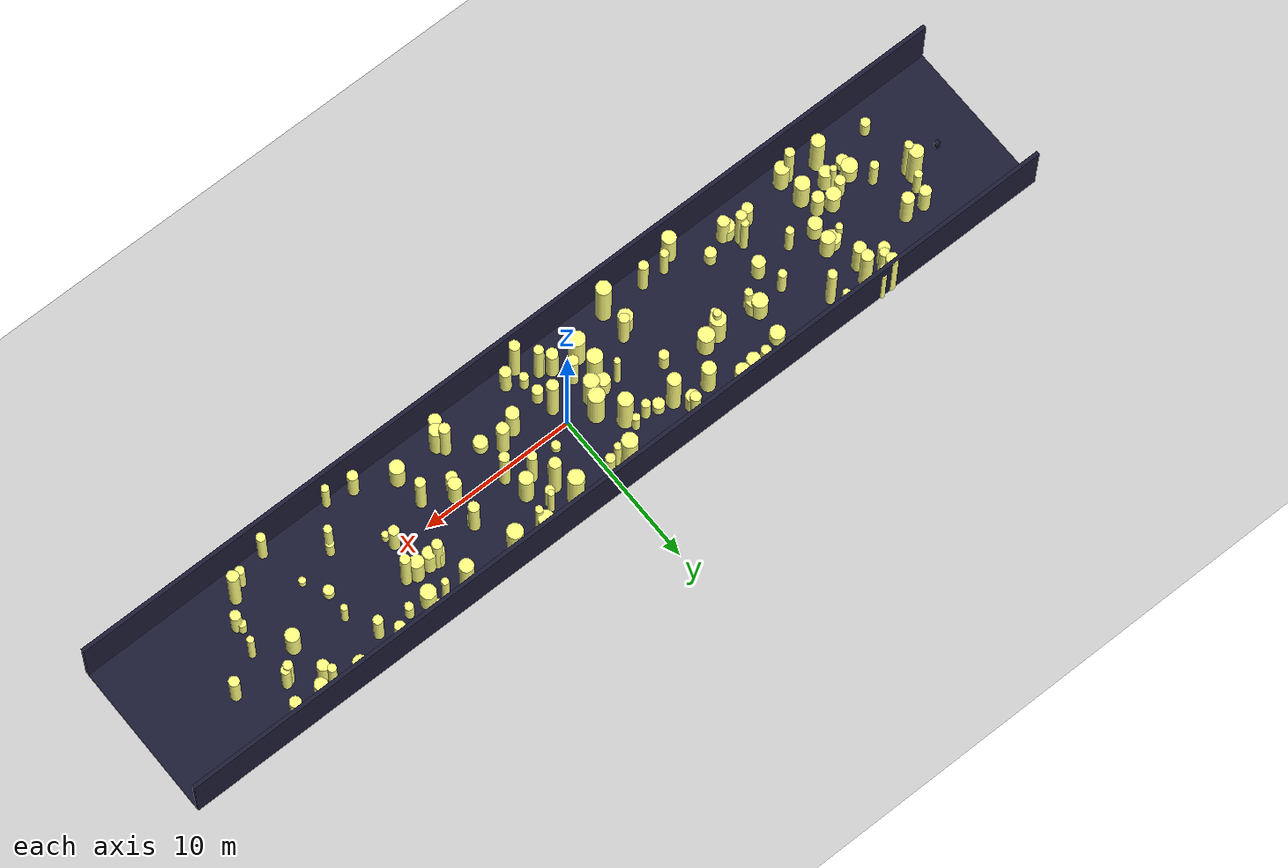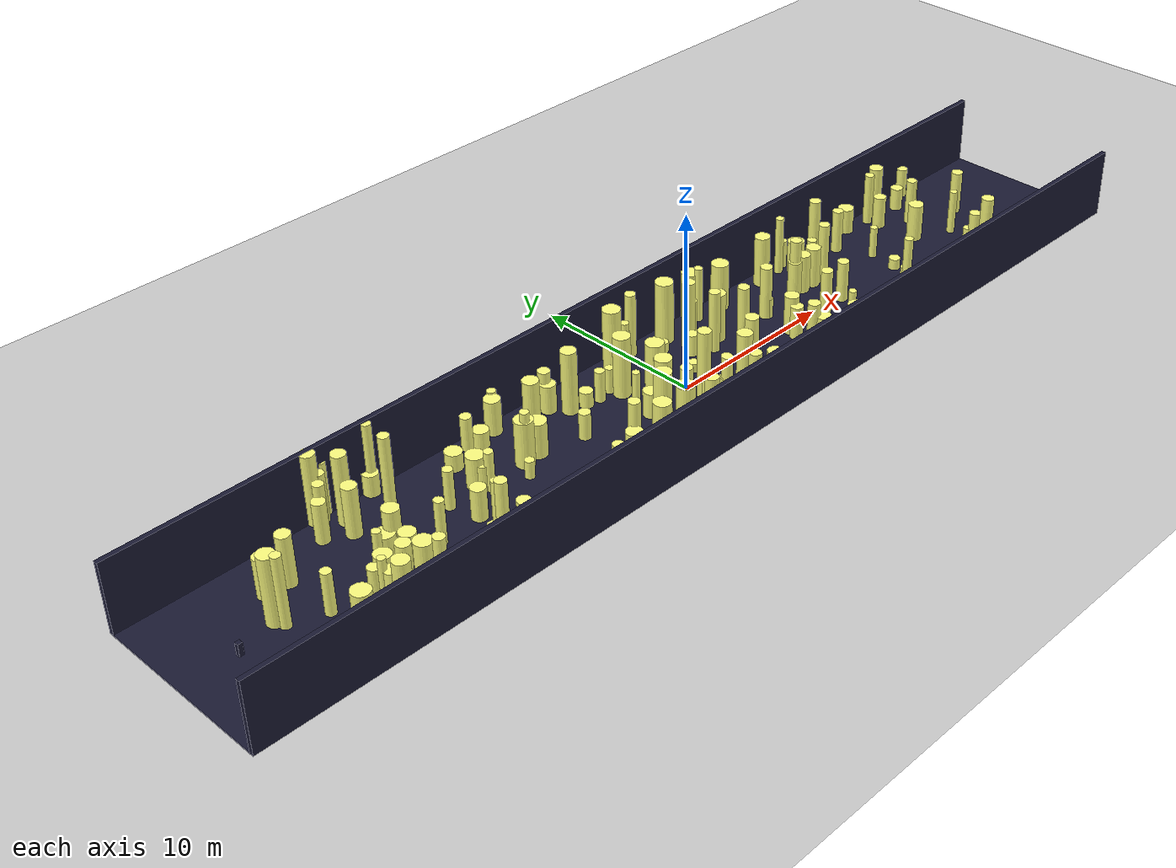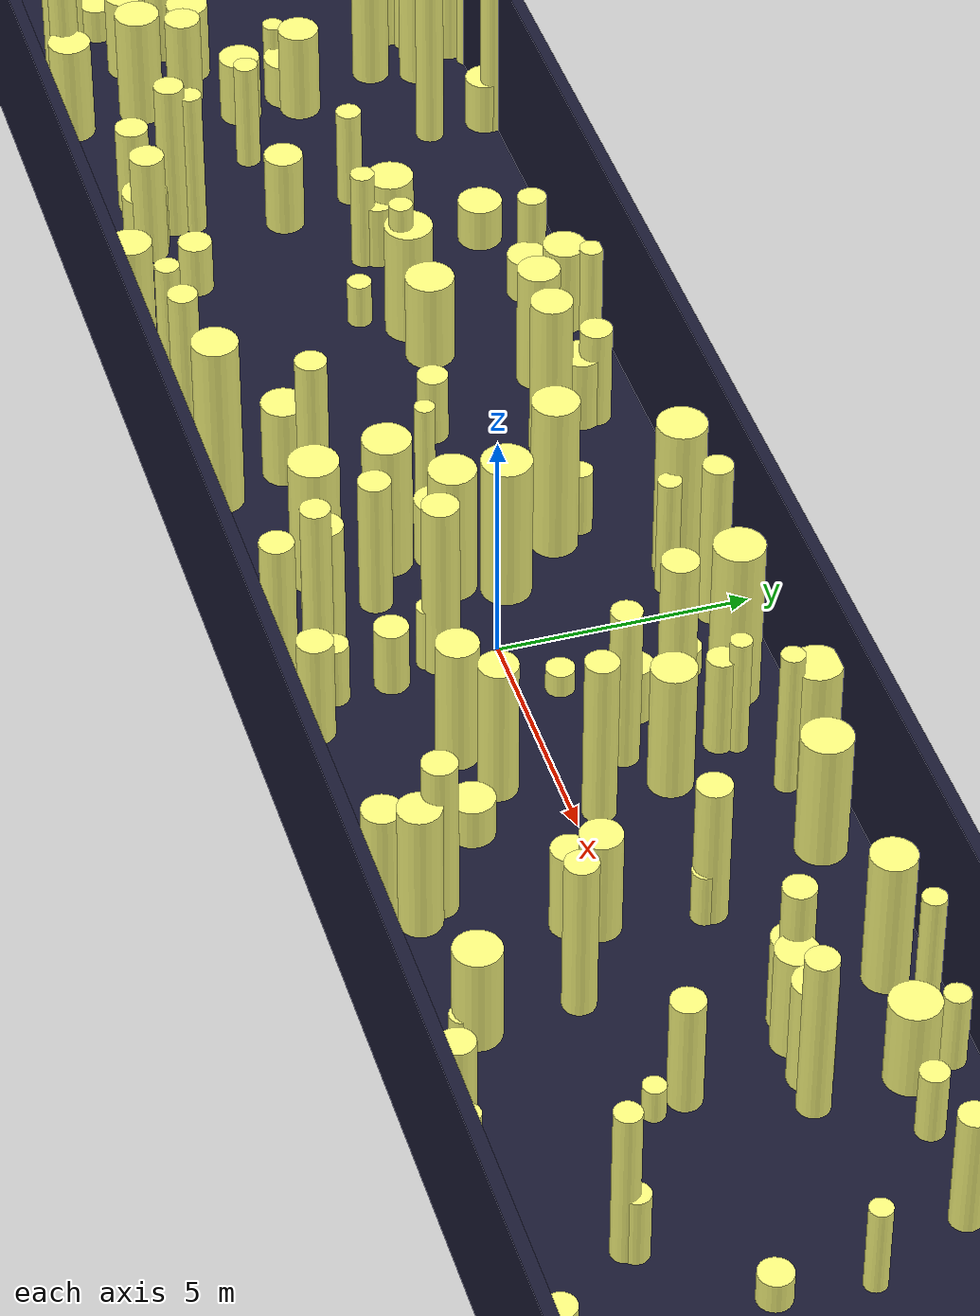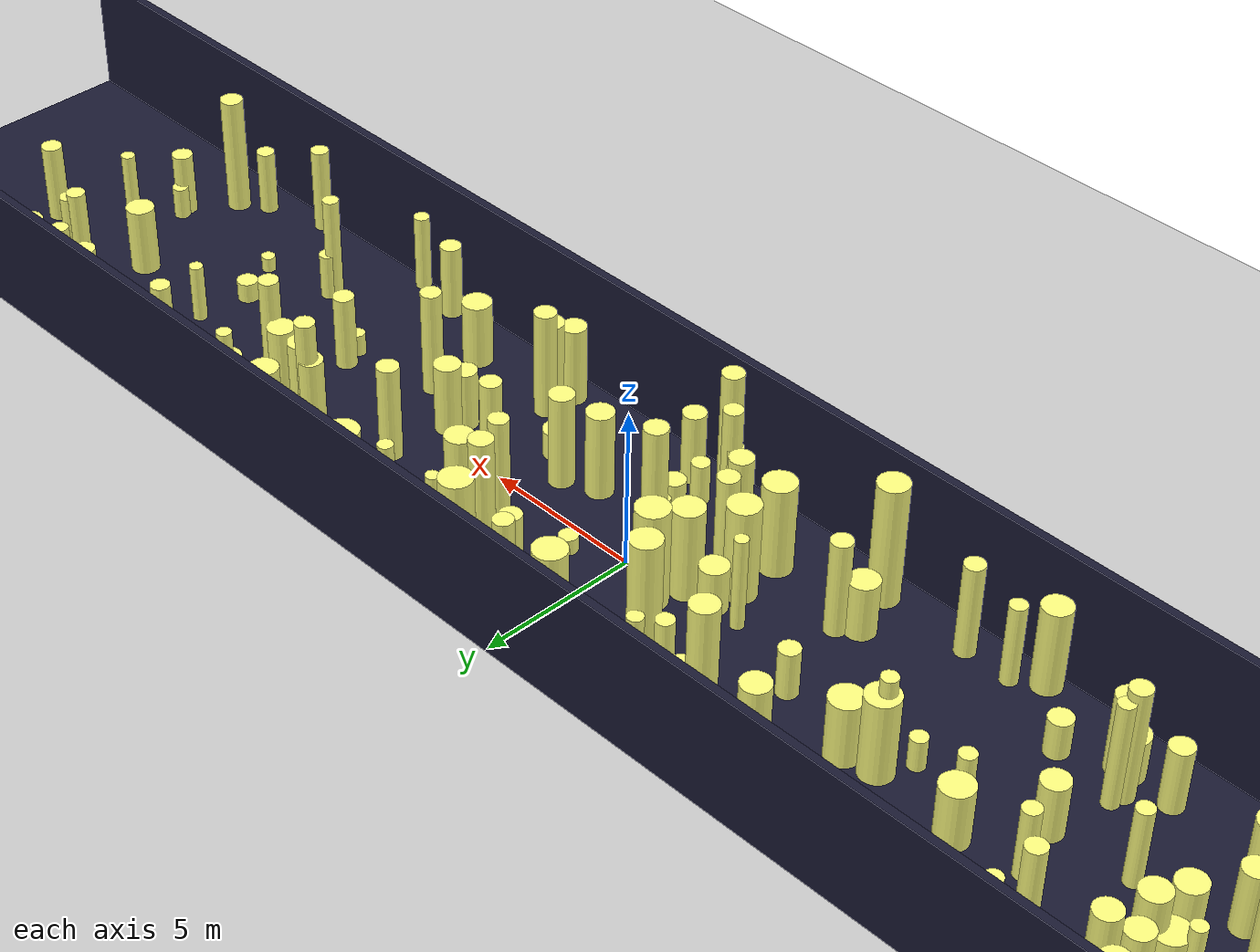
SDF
<?xml version="1.0"?>
<sdf version="1.4">
  <world name="default">
    <gui>
      <camera name="user_camera">
        <pose>-20 -30 40 0 0.66 0.83</pose>
      </camera>
    </gui>
    <include>
      <uri>model://ground_plane</uri>
    </include>
    <include>
      <uri>model://sun</uri>
    </include>
    <scene>
      <shadows>0</shadows>
    </scene>
    <model name="forest">
      <static>true</static>
      <link name="cylinder0">
        <pose>-12.502721954358915 -2.6659656342065974 0.6085833904426031 0 0 0 </pose>
        <visual name="visual">
          <geometry>
            <cylinder>
              <radius>0.3510681015145204</radius>
              <length>1.2171667808852062</length>
            </cylinder>
          </geometry>
          <material>
            <ambient>0.6 0.6 0.6 1</ambient>
            <diffuse>1 1 0.5 1</diffuse>
            <specular>0 0 0</specular>
            <emissive>0 0 0 1</emissive>
          </material>
        </visual>
        <collision name="collision">
          <geometry>
            <cylinder>
              <radius>0.3510681015145204</radius>
              <length>1.2171667808852062</length>
            </cylinder>
          </geometry>
          <max_contacts>0</max_contacts>
        </collision>
      </link>
      <link name="cylinder1">
        <pose>15.326810881068745 4.44815020159648 1.5245089961670204 0 0 0 </pose>
        <visual name="visual">
          <geometry>
            <cylinder>
              <radius>0.32884276525468004</radius>
              <length>3.049017992334041</length>
            </cylinder>
          </geometry>
          <material>
            <ambient>0.6 0.6 0.6 1</ambient>
            <diffuse>1 1 0.5 1</diffuse>
            <specular>0 0 0</specular>
            <emissive>0 0 0 1</emissive>
          </material>
        </visual>
        <collision name="collision">
          <geometry>
            <cylinder>
              <radius>0.32884276525468004</radius>
              <length>3.049017992334041</length>
            </cylinder>
          </geometry>
          <max_contacts>0</max_contacts>
        </collision>
      </link>
      <link name="cylinder2">
        <pose>-18.162453601790588 -0.2444685721580253 0.7804369950678622 0 0 0 </pose>
        <visual name="visual">
          <geometry>
            <cylinder>
              <radius>0.4354509630093727</radius>
              <length>1.5608739901357245</length>
            </cylinder>
          </geometry>
          <material>
            <ambient>0.6 0.6 0.6 1</ambient>
            <diffuse>1 1 0.5 1</diffuse>
            <specular>0 0 0</specular>
            <emissive>0 0 0 1</emissive>
          </material>
        </visual>
        <collision name="collision">
          <geometry>
            <cylinder>
              <radius>0.4354509630093727</radius>
              <length>1.5608739901357245</length>
            </cylinder>
          </geometry>
          <max_contacts>0</max_contacts>
        </collision>
      </link>
      <link name="cylinder3">
        <pose>-8.564383305479438 -3.849886137093559 1.5123958988349284 0 0 0 </pose>
        <visual name="visual">
          <geometry>
            <cylinder>
              <radius>0.30243147252921776</radius>
              <length>3.024791797669857</length>
            </cylinder>
          </geometry>
          <material>
            <ambient>0.6 0.6 0.6 1</ambient>
            <diffuse>1 1 0.5 1</diffuse>
            <specular>0 0 0</specular>
            <emissive>0 0 0 1</emissive>
          </material>
        </visual>
        <collision name="collision">
          <geometry>
            <cylinder>
              <radius>0.30243147252921776</radius>
              <length>3.024791797669857</length>
            </cylinder>
          </geometry>
          <max_contacts>0</max_contacts>
        </collision>
      </link>
      <link name="cylinder4">
        <pose>-2.900554031618597 2.557931823986218 0.7568684038138516 0 0 0 </pose>
        <visual name="visual">
          <geometry>
            <cylinder>
              <radius>0.23991858585969472</radius>
              <length>1.5137368076277031</length>
            </cylinder>
          </geometry>
          <material>
            <ambient>0.6 0.6 0.6 1</ambient>
            <diffuse>1 1 0.5 1</diffuse>
            <specular>0 0 0</specular>
            <emissive>0 0 0 1</emissive>
          </material>
        </visual>
        <collision name="collision">
          <geometry>
            <cylinder>
              <radius>0.23991858585969472</radius>
              <length>1.5137368076277031</length>
            </cylinder>
          </geometry>
          <max_contacts>0</max_contacts>
        </collision>
      </link>
      <link name="cylinder5">
        <pose>1.313964049926085 -3.8849885170803002 1.1643307283110613 0 0 0 </pose>
        <visual name="visual">
          <geometry>
            <cylinder>
              <radius>0.34957092293422487</radius>
              <length>2.3286614566221226</length>
            </cylinder>
          </geometry>
          <material>
            <ambient>0.6 0.6 0.6 1</ambient>
            <diffuse>1 1 0.5 1</diffuse>
            <specular>0 0 0</specular>
            <emissive>0 0 0 1</emissive>
          </material>
        </visual>
        <collision name="collision">
          <geometry>
            <cylinder>
              <radius>0.34957092293422487</radius>
              <length>2.3286614566221226</length>
            </cylinder>
          </geometry>
          <max_contacts>0</max_contacts>
        </collision>
      </link>
      <link name="cylinder6">
        <pose>-15.604253564923754 -3.2093322992431625 1.0340001270067756 0 0 0 </pose>
        <visual name="visual">
          <geometry>
            <cylinder>
              <radius>0.3472464015730837</radius>
              <length>2.068000254013551</length>
            </cylinder>
          </geometry>
          <material>
            <ambient>0.6 0.6 0.6 1</ambient>
            <diffuse>1 1 0.5 1</diffuse>
            <specular>0 0 0</specular>
            <emissive>0 0 0 1</emissive>
          </material>
        </visual>
        <collision name="collision">
          <geometry>
            <cylinder>
              <radius>0.3472464015730837</radius>
              <length>2.068000254013551</length>
            </cylinder>
          </geometry>
          <max_contacts>0</max_contacts>
        </collision>
      </link>
      <link name="cylinder7">
        <pose>-24.395725136393526 -3.3159768479499006 0.6917096451607068 0 0 0 </pose>
        <visual name="visual">
          <geometry>
            <cylinder>
              <radius>0.29855471631764946</radius>
              <length>1.3834192903214135</length>
            </cylinder>
          </geometry>
          <material>
            <ambient>0.6 0.6 0.6 1</ambient>
            <diffuse>1 1 0.5 1</diffuse>
            <specular>0 0 0</specular>
            <emissive>0 0 0 1</emissive>
          </material>
        </visual>
        <collision name="collision">
          <geometry>
            <cylinder>
              <radius>0.29855471631764946</radius>
              <length>1.3834192903214135</length>
            </cylinder>
          </geometry>
          <max_contacts>0</max_contacts>
        </collision>
      </link>
      <link name="cylinder8">
        <pose>3.702451197373353 -1.1173654504020272 1.5423725622052054 0 0 0 </pose>
        <visual name="visual">
          <geometry>
            <cylinder>
              <radius>0.3797419441660974</radius>
              <length>3.0847451244104107</length>
            </cylinder>
          </geometry>
          <material>
            <ambient>0.6 0.6 0.6 1</ambient>
            <diffuse>1 1 0.5 1</diffuse>
            <specular>0 0 0</specular>
            <emissive>0 0 0 1</emissive>
          </material>
        </visual>
        <collision name="collision">
          <geometry>
            <cylinder>
              <radius>0.3797419441660974</radius>
              <length>3.0847451244104107</length>
            </cylinder>
          </geometry>
          <max_contacts>0</max_contacts>
        </collision>
      </link>
      <link name="cylinder9">
        <pose>-24.634450793001072 0.05189174106900296 1.98661205535265 0 0 0 </pose>
        <visual name="visual">
          <geometry>
            <cylinder>
              <radius>0.2565379622526275</radius>
              <length>3.9732241107053</length>
            </cylinder>
          </geometry>
          <material>
            <ambient>0.6 0.6 0.6 1</ambient>
            <diffuse>1 1 0.5 1</diffuse>
            <specular>0 0 0</specular>
            <emissive>0 0 0 1</emissive>
          </material>
        </visual>
        <collision name="collision">
          <geometry>
            <cylinder>
              <radius>0.2565379622526275</radius>
              <length>3.9732241107053</length>
            </cylinder>
          </geometry>
          <max_contacts>0</max_contacts>
        </collision>
      </link>
      <link name="cylinder10">
        <pose>-0.7432844458045196 3.606858276507017 1.3522364615848521 0 0 0 </pose>
        <visual name="visual">
          <geometry>
            <cylinder>
              <radius>0.2308794543132723</radius>
              <length>2.7044729231697042</length>
            </cylinder>
          </geometry>
          <material>
            <ambient>0.6 0.6 0.6 1</ambient>
            <diffuse>1 1 0.5 1</diffuse>
            <specular>0 0 0</specular>
            <emissive>0 0 0 1</emissive>
          </material>
        </visual>
        <collision name="collision">
          <geometry>
            <cylinder>
              <radius>0.2308794543132723</radius>
              <length>2.7044729231697042</length>
            </cylinder>
          </geometry>
          <max_contacts>0</max_contacts>
        </collision>
      </link>
      <link name="cylinder11">
        <pose>-6.175850569645785 -2.4807912993549444 0.9096561768423661 0 0 0 </pose>
        <visual name="visual">
          <geometry>
            <cylinder>
              <radius>0.44854788550880226</radius>
              <length>1.8193123536847322</length>
            </cylinder>
          </geometry>
          <material>
            <ambient>0.6 0.6 0.6 1</ambient>
            <diffuse>1 1 0.5 1</diffuse>
            <specular>0 0 0</specular>
            <emissive>0 0 0 1</emissive>
          </material>
        </visual>
        <collision name="collision">
          <geometry>
            <cylinder>
              <radius>0.44854788550880226</radius>
              <length>1.8193123536847322</length>
            </cylinder>
          </geometry>
          <max_contacts>0</max_contacts>
        </collision>
      </link>
      <link name="cylinder12">
        <pose>11.851252865154429 4.0846548338123 1.7340153190742436 0 0 0 </pose>
        <visual name="visual">
          <geometry>
            <cylinder>
              <radius>0.225802921579659</radius>
              <length>3.468030638148487</length>
            </cylinder>
          </geometry>
          <material>
            <ambient>0.6 0.6 0.6 1</ambient>
            <diffuse>1 1 0.5 1</diffuse>
            <specular>0 0 0</specular>
            <emissive>0 0 0 1</emissive>
          </material>
        </visual>
        <collision name="collision">
          <geometry>
            <cylinder>
              <radius>0.225802921579659</radius>
              <length>3.468030638148487</length>
            </cylinder>
          </geometry>
          <max_contacts>0</max_contacts>
        </collision>
      </link>
      <link name="cylinder13">
        <pose>9.528915182945973 -3.262580325282216 1.0667924906563833 0 0 0 </pose>
        <visual name="visual">
          <geometry>
            <cylinder>
              <radius>0.45164004948687075</radius>
              <length>2.1335849813127665</length>
            </cylinder>
          </geometry>
          <material>
            <ambient>0.6 0.6 0.6 1</ambient>
            <diffuse>1 1 0.5 1</diffuse>
            <specular>0 0 0</specular>
            <emissive>0 0 0 1</emissive>
          </material>
        </visual>
        <collision name="collision">
          <geometry>
            <cylinder>
              <radius>0.45164004948687075</radius>
              <length>2.1335849813127665</length>
            </cylinder>
          </geometry>
          <max_contacts>0</max_contacts>
        </collision>
      </link>
      <link name="cylinder14">
        <pose>0.38465863244394427 -2.1824603545408303 0.7296094701448637 0 0 0 </pose>
        <visual name="visual">
          <geometry>
            <cylinder>
              <radius>0.3377690477103479</radius>
              <length>1.4592189402897273</length>
            </cylinder>
          </geometry>
          <material>
            <ambient>0.6 0.6 0.6 1</ambient>
            <diffuse>1 1 0.5 1</diffuse>
            <specular>0 0 0</specular>
            <emissive>0 0 0 1</emissive>
          </material>
        </visual>
        <collision name="collision">
          <geometry>
            <cylinder>
              <radius>0.3377690477103479</radius>
              <length>1.4592189402897273</length>
            </cylinder>
          </geometry>
          <max_contacts>0</max_contacts>
        </collision>
      </link>
      <link name="cylinder15">
        <pose>20.789859159138125 4.408615186613762 1.540305498436152 0 0 0 </pose>
        <visual name="visual">
          <geometry>
            <cylinder>
              <radius>0.3992713100745151</radius>
              <length>3.080610996872304</length>
            </cylinder>
          </geometry>
          <material>
            <ambient>0.6 0.6 0.6 1</ambient>
            <diffuse>1 1 0.5 1</diffuse>
            <specular>0 0 0</specular>
            <emissive>0 0 0 1</emissive>
          </material>
        </visual>
        <collision name="collision">
          <geometry>
            <cylinder>
              <radius>0.3992713100745151</radius>
              <length>3.080610996872304</length>
            </cylinder>
          </geometry>
          <max_contacts>0</max_contacts>
        </collision>
      </link>
      <link name="cylinder16">
        <pose>-1.9539033908960448 -0.29834200253286536 1.4721334536363095 0 0 0 </pose>
        <visual name="visual">
          <geometry>
            <cylinder>
              <radius>0.47072366416954475</radius>
              <length>2.944266907272619</length>
            </cylinder>
          </geometry>
          <material>
            <ambient>0.6 0.6 0.6 1</ambient>
            <diffuse>1 1 0.5 1</diffuse>
            <specular>0 0 0</specular>
            <emissive>0 0 0 1</emissive>
          </material>
        </visual>
        <collision name="collision">
          <geometry>
            <cylinder>
              <radius>0.47072366416954475</radius>
              <length>2.944266907272619</length>
            </cylinder>
          </geometry>
          <max_contacts>0</max_contacts>
        </collision>
      </link>
      <link name="cylinder17">
        <pose>22.17317977526671 -0.17076089515016335 1.340687301200209 0 0 0 </pose>
        <visual name="visual">
          <geometry>
            <cylinder>
              <radius>0.21578449378087355</radius>
              <length>2.681374602400418</length>
            </cylinder>
          </geometry>
          <material>
            <ambient>0.6 0.6 0.6 1</ambient>
            <diffuse>1 1 0.5 1</diffuse>
            <specular>0 0 0</specular>
            <emissive>0 0 0 1</emissive>
          </material>
        </visual>
        <collision name="collision">
          <geometry>
            <cylinder>
              <radius>0.21578449378087355</radius>
              <length>2.681374602400418</length>
            </cylinder>
          </geometry>
          <max_contacts>0</max_contacts>
        </collision>
      </link>
      <link name="cylinder18">
        <pose>10.749598188778428 1.991703804756165 1.025701142250085 0 0 0 </pose>
        <visual name="visual">
          <geometry>
            <cylinder>
              <radius>0.3834756503450859</radius>
              <length>2.05140228450017</length>
            </cylinder>
          </geometry>
          <material>
            <ambient>0.6 0.6 0.6 1</ambient>
            <diffuse>1 1 0.5 1</diffuse>
            <specular>0 0 0</specular>
            <emissive>0 0 0 1</emissive>
          </material>
        </visual>
        <collision name="collision">
          <geometry>
            <cylinder>
              <radius>0.3834756503450859</radius>
              <length>2.05140228450017</length>
            </cylinder>
          </geometry>
          <max_contacts>0</max_contacts>
        </collision>
      </link>
      <link name="cylinder19">
        <pose>-3.765693110406204 2.355463253587745 0.9191963411689219 0 0 0 </pose>
        <visual name="visual">
          <geometry>
            <cylinder>
              <radius>0.2706350855969597</radius>
              <length>1.8383926823378438</length>
            </cylinder>
          </geometry>
          <material>
            <ambient>0.6 0.6 0.6 1</ambient>
            <diffuse>1 1 0.5 1</diffuse>
            <specular>0 0 0</specular>
            <emissive>0 0 0 1</emissive>
          </material>
        </visual>
        <collision name="collision">
          <geometry>
            <cylinder>
              <radius>0.2706350855969597</radius>
              <length>1.8383926823378438</length>
            </cylinder>
          </geometry>
          <max_contacts>0</max_contacts>
        </collision>
      </link>
      <link name="cylinder20">
        <pose>-19.49257124488244 4.815404987633817 1.9871582576625482 0 0 0 </pose>
        <visual name="visual">
          <geometry>
            <cylinder>
              <radius>0.38212930709392834</radius>
              <length>3.9743165153250963</length>
            </cylinder>
          </geometry>
          <material>
            <ambient>0.6 0.6 0.6 1</ambient>
            <diffuse>1 1 0.5 1</diffuse>
            <specular>0 0 0</specular>
            <emissive>0 0 0 1</emissive>
          </material>
        </visual>
        <collision name="collision">
          <geometry>
            <cylinder>
              <radius>0.38212930709392834</radius>
              <length>3.9743165153250963</length>
            </cylinder>
          </geometry>
          <max_contacts>0</max_contacts>
        </collision>
      </link>
      <link name="cylinder21">
        <pose>-6.465806620505148 0.6290368193749618 0.784559223407981 0 0 0 </pose>
        <visual name="visual">
          <geometry>
            <cylinder>
              <radius>0.3131240611195635</radius>
              <length>1.569118446815962</length>
            </cylinder>
          </geometry>
          <material>
            <ambient>0.6 0.6 0.6 1</ambient>
            <diffuse>1 1 0.5 1</diffuse>
            <specular>0 0 0</specular>
            <emissive>0 0 0 1</emissive>
          </material>
        </visual>
        <collision name="collision">
          <geometry>
            <cylinder>
              <radius>0.3131240611195635</radius>
              <length>1.569118446815962</length>
            </cylinder>
          </geometry>
          <max_contacts>0</max_contacts>
        </collision>
      </link>
      <link name="cylinder22">
        <pose>21.6921501270242 -1.6663580762201633 0.5468895035778689 0 0 0 </pose>
        <visual name="visual">
          <geometry>
            <cylinder>
              <radius>0.24838409049166843</radius>
              <length>1.0937790071557378</length>
            </cylinder>
          </geometry>
          <material>
            <ambient>0.6 0.6 0.6 1</ambient>
            <diffuse>1 1 0.5 1</diffuse>
            <specular>0 0 0</specular>
            <emissive>0 0 0 1</emissive>
          </material>
        </visual>
        <collision name="collision">
          <geometry>
            <cylinder>
              <radius>0.24838409049166843</radius>
              <length>1.0937790071557378</length>
            </cylinder>
          </geometry>
          <max_contacts>0</max_contacts>
        </collision>
      </link>
      <link name="cylinder23">
        <pose>20.137798298450257 0.9372512442738916 1.1237016619375413 0 0 0 </pose>
        <visual name="visual">
          <geometry>
            <cylinder>
              <radius>0.4350848166733843</radius>
              <length>2.2474033238750826</length>
            </cylinder>
          </geometry>
          <material>
            <ambient>0.6 0.6 0.6 1</ambient>
            <diffuse>1 1 0.5 1</diffuse>
            <specular>0 0 0</specular>
            <emissive>0 0 0 1</emissive>
          </material>
        </visual>
        <collision name="collision">
          <geometry>
            <cylinder>
              <radius>0.4350848166733843</radius>
              <length>2.2474033238750826</length>
            </cylinder>
          </geometry>
          <max_contacts>0</max_contacts>
        </collision>
      </link>
      <link name="cylinder24">
        <pose>2.6504902617085655 -1.5724567202440998 1.4095039634519797 0 0 0 </pose>
        <visual name="visual">
          <geometry>
            <cylinder>
              <radius>0.411862540570846</radius>
              <length>2.8190079269039594</length>
            </cylinder>
          </geometry>
          <material>
            <ambient>0.6 0.6 0.6 1</ambient>
            <diffuse>1 1 0.5 1</diffuse>
            <specular>0 0 0</specular>
            <emissive>0 0 0 1</emissive>
          </material>
        </visual>
        <collision name="collision">
          <geometry>
            <cylinder>
              <radius>0.411862540570846</radius>
              <length>2.8190079269039594</length>
            </cylinder>
          </geometry>
          <max_contacts>0</max_contacts>
        </collision>
      </link>
      <link name="cylinder25">
        <pose>-22.87648430715794 2.2072677745387717 1.423964659570777 0 0 0 </pose>
        <visual name="visual">
          <geometry>
            <cylinder>
              <radius>0.38179037752833966</radius>
              <length>2.847929319141554</length>
            </cylinder>
          </geometry>
          <material>
            <ambient>0.6 0.6 0.6 1</ambient>
            <diffuse>1 1 0.5 1</diffuse>
            <specular>0 0 0</specular>
            <emissive>0 0 0 1</emissive>
          </material>
        </visual>
        <collision name="collision">
          <geometry>
            <cylinder>
              <radius>0.38179037752833966</radius>
              <length>2.847929319141554</length>
            </cylinder>
          </geometry>
          <max_contacts>0</max_contacts>
        </collision>
      </link>
      <link name="cylinder26">
        <pose>19.833739490549426 3.294432998006373 0.9844088126925716 0 0 0 </pose>
        <visual name="visual">
          <geometry>
            <cylinder>
              <radius>0.3623249942571851</radius>
              <length>1.9688176253851433</length>
            </cylinder>
          </geometry>
          <material>
            <ambient>0.6 0.6 0.6 1</ambient>
            <diffuse>1 1 0.5 1</diffuse>
            <specular>0 0 0</specular>
            <emissive>0 0 0 1</emissive>
          </material>
        </visual>
        <collision name="collision">
          <geometry>
            <cylinder>
              <radius>0.3623249942571851</radius>
              <length>1.9688176253851433</length>
            </cylinder>
          </geometry>
          <max_contacts>0</max_contacts>
        </collision>
      </link>
      <link name="cylinder27">
        <pose>0.030223723886287246 -1.3574997205438324 0.729812917239677 0 0 0 </pose>
        <visual name="visual">
          <geometry>
            <cylinder>
              <radius>0.23898480077361903</radius>
              <length>1.459625834479354</length>
            </cylinder>
          </geometry>
          <material>
            <ambient>0.6 0.6 0.6 1</ambient>
            <diffuse>1 1 0.5 1</diffuse>
            <specular>0 0 0</specular>
            <emissive>0 0 0 1</emissive>
          </material>
        </visual>
        <collision name="collision">
          <geometry>
            <cylinder>
              <radius>0.23898480077361903</radius>
              <length>1.459625834479354</length>
            </cylinder>
          </geometry>
          <max_contacts>0</max_contacts>
        </collision>
      </link>
      <link name="cylinder28">
        <pose>13.511106060946105 -4.632045625972444 1.276704302045779 0 0 0 </pose>
        <visual name="visual">
          <geometry>
            <cylinder>
              <radius>0.24020327871995664</radius>
              <length>2.553408604091558</length>
            </cylinder>
          </geometry>
          <material>
            <ambient>0.6 0.6 0.6 1</ambient>
            <diffuse>1 1 0.5 1</diffuse>
            <specular>0 0 0</specular>
            <emissive>0 0 0 1</emissive>
          </material>
        </visual>
        <collision name="collision">
          <geometry>
            <cylinder>
              <radius>0.24020327871995664</radius>
              <length>2.553408604091558</length>
            </cylinder>
          </geometry>
          <max_contacts>0</max_contacts>
        </collision>
      </link>
      <link name="cylinder29">
        <pose>20.902014358298864 -3.3283581596672986 1.9682573430151837 0 0 0 </pose>
        <visual name="visual">
          <geometry>
            <cylinder>
              <radius>0.35390016411605674</radius>
              <length>3.9365146860303675</length>
            </cylinder>
          </geometry>
          <material>
            <ambient>0.6 0.6 0.6 1</ambient>
            <diffuse>1 1 0.5 1</diffuse>
            <specular>0 0 0</specular>
            <emissive>0 0 0 1</emissive>
          </material>
        </visual>
        <collision name="collision">
          <geometry>
            <cylinder>
              <radius>0.35390016411605674</radius>
              <length>3.9365146860303675</length>
            </cylinder>
          </geometry>
          <max_contacts>0</max_contacts>
        </collision>
      </link>
      <link name="cylinder30">
        <pose>-12.437484253757225 3.403493577080285 0.5104835917112851 0 0 0 </pose>
        <visual name="visual">
          <geometry>
            <cylinder>
              <radius>0.4584076746730561</radius>
              <length>1.0209671834225702</length>
            </cylinder>
          </geometry>
          <material>
            <ambient>0.6 0.6 0.6 1</ambient>
            <diffuse>1 1 0.5 1</diffuse>
            <specular>0 0 0</specular>
            <emissive>0 0 0 1</emissive>
          </material>
        </visual>
        <collision name="collision">
          <geometry>
            <cylinder>
              <radius>0.4584076746730561</radius>
              <length>1.0209671834225702</length>
            </cylinder>
          </geometry>
          <max_contacts>0</max_contacts>
        </collision>
      </link>
      <link name="cylinder31">
        <pose>-5.7248087732027955 -3.898096598784978 1.9844881413474247 0 0 0 </pose>
        <visual name="visual">
          <geometry>
            <cylinder>
              <radius>0.4616749639141078</radius>
              <length>3.9689762826948494</length>
            </cylinder>
          </geometry>
          <material>
            <ambient>0.6 0.6 0.6 1</ambient>
            <diffuse>1 1 0.5 1</diffuse>
            <specular>0 0 0</specular>
            <emissive>0 0 0 1</emissive>
          </material>
        </visual>
        <collision name="collision">
          <geometry>
            <cylinder>
              <radius>0.4616749639141078</radius>
              <length>3.9689762826948494</length>
            </cylinder>
          </geometry>
          <max_contacts>0</max_contacts>
        </collision>
      </link>
      <link name="cylinder32">
        <pose>-2.612749098027951 1.9390665615845082 1.7797026861179794 0 0 0 </pose>
        <visual name="visual">
          <geometry>
            <cylinder>
              <radius>0.46663268230172333</radius>
              <length>3.559405372235959</length>
            </cylinder>
          </geometry>
          <material>
            <ambient>0.6 0.6 0.6 1</ambient>
            <diffuse>1 1 0.5 1</diffuse>
            <specular>0 0 0</specular>
            <emissive>0 0 0 1</emissive>
          </material>
        </visual>
        <collision name="collision">
          <geometry>
            <cylinder>
              <radius>0.46663268230172333</radius>
              <length>3.559405372235959</length>
            </cylinder>
          </geometry>
          <max_contacts>0</max_contacts>
        </collision>
      </link>
      <link name="cylinder33">
        <pose>10.277843832452142 3.9662285758313267 1.5198597949279122 0 0 0 </pose>
        <visual name="visual">
          <geometry>
            <cylinder>
              <radius>0.43222622895694485</radius>
              <length>3.0397195898558245</length>
            </cylinder>
          </geometry>
          <material>
            <ambient>0.6 0.6 0.6 1</ambient>
            <diffuse>1 1 0.5 1</diffuse>
            <specular>0 0 0</specular>
            <emissive>0 0 0 1</emissive>
          </material>
        </visual>
        <collision name="collision">
          <geometry>
            <cylinder>
              <radius>0.43222622895694485</radius>
              <length>3.0397195898558245</length>
            </cylinder>
          </geometry>
          <max_contacts>0</max_contacts>
        </collision>
      </link>
      <link name="cylinder34">
        <pose>6.341370451103096 -2.992066850662254 1.7665536685939367 0 0 0 </pose>
        <visual name="visual">
          <geometry>
            <cylinder>
              <radius>0.3342498121226667</radius>
              <length>3.5331073371878734</length>
            </cylinder>
          </geometry>
          <material>
            <ambient>0.6 0.6 0.6 1</ambient>
            <diffuse>1 1 0.5 1</diffuse>
            <specular>0 0 0</specular>
            <emissive>0 0 0 1</emissive>
          </material>
        </visual>
        <collision name="collision">
          <geometry>
            <cylinder>
              <radius>0.3342498121226667</radius>
              <length>3.5331073371878734</length>
            </cylinder>
          </geometry>
          <max_contacts>0</max_contacts>
        </collision>
      </link>
      <link name="cylinder35">
        <pose>12.031115373614448 -0.32621599096671083 1.2311138491603326 0 0 0 </pose>
        <visual name="visual">
          <geometry>
            <cylinder>
              <radius>0.32083398046830275</radius>
              <length>2.4622276983206652</length>
            </cylinder>
          </geometry>
          <material>
            <ambient>0.6 0.6 0.6 1</ambient>
            <diffuse>1 1 0.5 1</diffuse>
            <specular>0 0 0</specular>
            <emissive>0 0 0 1</emissive>
          </material>
        </visual>
        <collision name="collision">
          <geometry>
            <cylinder>
              <radius>0.32083398046830275</radius>
              <length>2.4622276983206652</length>
            </cylinder>
          </geometry>
          <max_contacts>0</max_contacts>
        </collision>
      </link>
      <link name="cylinder36">
        <pose>-1.5742121338384827 0.6539919885100796 1.617637387164022 0 0 0 </pose>
        <visual name="visual">
          <geometry>
            <cylinder>
              <radius>0.4964075488692837</radius>
              <length>3.235274774328044</length>
            </cylinder>
          </geometry>
          <material>
            <ambient>0.6 0.6 0.6 1</ambient>
            <diffuse>1 1 0.5 1</diffuse>
            <specular>0 0 0</specular>
            <emissive>0 0 0 1</emissive>
          </material>
        </visual>
        <collision name="collision">
          <geometry>
            <cylinder>
              <radius>0.4964075488692837</radius>
              <length>3.235274774328044</length>
            </cylinder>
          </geometry>
          <max_contacts>0</max_contacts>
        </collision>
      </link>
      <link name="cylinder37">
        <pose>23.703867928985538 4.6543589916086265 0.9164790352000004 0 0 0 </pose>
        <visual name="visual">
          <geometry>
            <cylinder>
              <radius>0.3063984760092656</radius>
              <length>1.8329580704000008</length>
            </cylinder>
          </geometry>
          <material>
            <ambient>0.6 0.6 0.6 1</ambient>
            <diffuse>1 1 0.5 1</diffuse>
            <specular>0 0 0</specular>
            <emissive>0 0 0 1</emissive>
          </material>
        </visual>
        <collision name="collision">
          <geometry>
            <cylinder>
              <radius>0.3063984760092656</radius>
              <length>1.8329580704000008</length>
            </cylinder>
          </geometry>
          <max_contacts>0</max_contacts>
        </collision>
      </link>
      <link name="cylinder38">
        <pose>-10.054779706547345 -3.8103376774504296 1.3178086906775555 0 0 0 </pose>
        <visual name="visual">
          <geometry>
            <cylinder>
              <radius>0.25343044838977596</radius>
              <length>2.635617381355111</length>
            </cylinder>
          </geometry>
          <material>
            <ambient>0.6 0.6 0.6 1</ambient>
            <diffuse>1 1 0.5 1</diffuse>
            <specular>0 0 0</specular>
            <emissive>0 0 0 1</emissive>
          </material>
        </visual>
        <collision name="collision">
          <geometry>
            <cylinder>
              <radius>0.25343044838977596</radius>
              <length>2.635617381355111</length>
            </cylinder>
          </geometry>
          <max_contacts>0</max_contacts>
        </collision>
      </link>
      <link name="cylinder39">
        <pose>19.744685019783738 4.060041109546567 1.5626195724777552 0 0 0 </pose>
        <visual name="visual">
          <geometry>
            <cylinder>
              <radius>0.2643367503565982</radius>
              <length>3.1252391449555104</length>
            </cylinder>
          </geometry>
          <material>
            <ambient>0.6 0.6 0.6 1</ambient>
            <diffuse>1 1 0.5 1</diffuse>
            <specular>0 0 0</specular>
            <emissive>0 0 0 1</emissive>
          </material>
        </visual>
        <collision name="collision">
          <geometry>
            <cylinder>
              <radius>0.2643367503565982</radius>
              <length>3.1252391449555104</length>
            </cylinder>
          </geometry>
          <max_contacts>0</max_contacts>
        </collision>
      </link>
      <link name="cylinder40">
        <pose>12.206433177939552 -0.9399574047651802 0.3850861844117669 0 0 0 </pose>
        <visual name="visual">
          <geometry>
            <cylinder>
              <radius>0.21621220133252175</radius>
              <length>0.7701723688235338</length>
            </cylinder>
          </geometry>
          <material>
            <ambient>0.6 0.6 0.6 1</ambient>
            <diffuse>1 1 0.5 1</diffuse>
            <specular>0 0 0</specular>
            <emissive>0 0 0 1</emissive>
          </material>
        </visual>
        <collision name="collision">
          <geometry>
            <cylinder>
              <radius>0.21621220133252175</radius>
              <length>0.7701723688235338</length>
            </cylinder>
          </geometry>
          <max_contacts>0</max_contacts>
        </collision>
      </link>
      <link name="cylinder41">
        <pose>4.68731782256253 -1.9014256234514848 0.46083601857654544 0 0 0 </pose>
        <visual name="visual">
          <geometry>
            <cylinder>
              <radius>0.4309551025935311</radius>
              <length>0.9216720371530909</length>
            </cylinder>
          </geometry>
          <material>
            <ambient>0.6 0.6 0.6 1</ambient>
            <diffuse>1 1 0.5 1</diffuse>
            <specular>0 0 0</specular>
            <emissive>0 0 0 1</emissive>
          </material>
        </visual>
        <collision name="collision">
          <geometry>
            <cylinder>
              <radius>0.4309551025935311</radius>
              <length>0.9216720371530909</length>
            </cylinder>
          </geometry>
          <max_contacts>0</max_contacts>
        </collision>
      </link>
      <link name="cylinder42">
        <pose>-18.82839487472479 2.847118229106637 1.428111722365252 0 0 0 </pose>
        <visual name="visual">
          <geometry>
            <cylinder>
              <radius>0.39076796356919996</radius>
              <length>2.856223444730504</length>
            </cylinder>
          </geometry>
          <material>
            <ambient>0.6 0.6 0.6 1</ambient>
            <diffuse>1 1 0.5 1</diffuse>
            <specular>0 0 0</specular>
            <emissive>0 0 0 1</emissive>
          </material>
        </visual>
        <collision name="collision">
          <geometry>
            <cylinder>
              <radius>0.39076796356919996</radius>
              <length>2.856223444730504</length>
            </cylinder>
          </geometry>
          <max_contacts>0</max_contacts>
        </collision>
      </link>
      <link name="cylinder43">
        <pose>-18.843256166601506 -2.2814033712467485 1.3097579532869124 0 0 0 </pose>
        <visual name="visual">
          <geometry>
            <cylinder>
              <radius>0.47332808294365725</radius>
              <length>2.6195159065738247</length>
            </cylinder>
          </geometry>
          <material>
            <ambient>0.6 0.6 0.6 1</ambient>
            <diffuse>1 1 0.5 1</diffuse>
            <specular>0 0 0</specular>
            <emissive>0 0 0 1</emissive>
          </material>
        </visual>
        <collision name="collision">
          <geometry>
            <cylinder>
              <radius>0.47332808294365725</radius>
              <length>2.6195159065738247</length>
            </cylinder>
          </geometry>
          <max_contacts>0</max_contacts>
        </collision>
      </link>
      <link name="cylinder44">
        <pose>16.854442063781235 1.3594188490321084 0.9549184677734529 0 0 0 </pose>
        <visual name="visual">
          <geometry>
            <cylinder>
              <radius>0.21280323200237297</radius>
              <length>1.9098369355469058</length>
            </cylinder>
          </geometry>
          <material>
            <ambient>0.6 0.6 0.6 1</ambient>
            <diffuse>1 1 0.5 1</diffuse>
            <specular>0 0 0</specular>
            <emissive>0 0 0 1</emissive>
          </material>
        </visual>
        <collision name="collision">
          <geometry>
            <cylinder>
              <radius>0.21280323200237297</radius>
              <length>1.9098369355469058</length>
            </cylinder>
          </geometry>
          <max_contacts>0</max_contacts>
        </collision>
      </link>
      <link name="cylinder45">
        <pose>-1.3032437107933568 -2.973867848958396 1.3769102334652517 0 0 0 </pose>
        <visual name="visual">
          <geometry>
            <cylinder>
              <radius>0.36313667066523897</radius>
              <length>2.7538204669305033</length>
            </cylinder>
          </geometry>
          <material>
            <ambient>0.6 0.6 0.6 1</ambient>
            <diffuse>1 1 0.5 1</diffuse>
            <specular>0 0 0</specular>
            <emissive>0 0 0 1</emissive>
          </material>
        </visual>
        <collision name="collision">
          <geometry>
            <cylinder>
              <radius>0.36313667066523897</radius>
              <length>2.7538204669305033</length>
            </cylinder>
          </geometry>
          <max_contacts>0</max_contacts>
        </collision>
      </link>
      <link name="cylinder46">
        <pose>-19.122946769099475 -3.8112538472455504 1.9331050397941834 0 0 0 </pose>
        <visual name="visual">
          <geometry>
            <cylinder>
              <radius>0.3000905206304188</radius>
              <length>3.8662100795883667</length>
            </cylinder>
          </geometry>
          <material>
            <ambient>0.6 0.6 0.6 1</ambient>
            <diffuse>1 1 0.5 1</diffuse>
            <specular>0 0 0</specular>
            <emissive>0 0 0 1</emissive>
          </material>
        </visual>
        <collision name="collision">
          <geometry>
            <cylinder>
              <radius>0.3000905206304188</radius>
              <length>3.8662100795883667</length>
            </cylinder>
          </geometry>
          <max_contacts>0</max_contacts>
        </collision>
      </link>
      <link name="cylinder47">
        <pose>-2.881032032274838 -0.36255889499444915 0.747176304831089 0 0 0 </pose>
        <visual name="visual">
          <geometry>
            <cylinder>
              <radius>0.4252923107288233</radius>
              <length>1.494352609662178</length>
            </cylinder>
          </geometry>
          <material>
            <ambient>0.6 0.6 0.6 1</ambient>
            <diffuse>1 1 0.5 1</diffuse>
            <specular>0 0 0</specular>
            <emissive>0 0 0 1</emissive>
          </material>
        </visual>
        <collision name="collision">
          <geometry>
            <cylinder>
              <radius>0.4252923107288233</radius>
              <length>1.494352609662178</length>
            </cylinder>
          </geometry>
          <max_contacts>0</max_contacts>
        </collision>
      </link>
      <link name="cylinder48">
        <pose>2.4846986057671145 1.9130466747569361 0.6471594099374249 0 0 0 </pose>
        <visual name="visual">
          <geometry>
            <cylinder>
              <radius>0.33719902281976466</radius>
              <length>1.2943188198748499</length>
            </cylinder>
          </geometry>
          <material>
            <ambient>0.6 0.6 0.6 1</ambient>
            <diffuse>1 1 0.5 1</diffuse>
            <specular>0 0 0</specular>
            <emissive>0 0 0 1</emissive>
          </material>
        </visual>
        <collision name="collision">
          <geometry>
            <cylinder>
              <radius>0.33719902281976466</radius>
              <length>1.2943188198748499</length>
            </cylinder>
          </geometry>
          <max_contacts>0</max_contacts>
        </collision>
      </link>
      <link name="cylinder49">
        <pose>7.855266788333395 1.547053276769228 1.5716414693703582 0 0 0 </pose>
        <visual name="visual">
          <geometry>
            <cylinder>
              <radius>0.33487286682670503</radius>
              <length>3.1432829387407164</length>
            </cylinder>
          </geometry>
          <material>
            <ambient>0.6 0.6 0.6 1</ambient>
            <diffuse>1 1 0.5 1</diffuse>
            <specular>0 0 0</specular>
            <emissive>0 0 0 1</emissive>
          </material>
        </visual>
        <collision name="collision">
          <geometry>
            <cylinder>
              <radius>0.33487286682670503</radius>
              <length>3.1432829387407164</length>
            </cylinder>
          </geometry>
          <max_contacts>0</max_contacts>
        </collision>
      </link>
      <link name="cylinder50">
        <pose>15.021751668879233 -2.3837789731522863 1.715162036652757 0 0 0 </pose>
        <visual name="visual">
          <geometry>
            <cylinder>
              <radius>0.2504492714636248</radius>
              <length>3.430324073305514</length>
            </cylinder>
          </geometry>
          <material>
            <ambient>0.6 0.6 0.6 1</ambient>
            <diffuse>1 1 0.5 1</diffuse>
            <specular>0 0 0</specular>
            <emissive>0 0 0 1</emissive>
          </material>
        </visual>
        <collision name="collision">
          <geometry>
            <cylinder>
              <radius>0.2504492714636248</radius>
              <length>3.430324073305514</length>
            </cylinder>
          </geometry>
          <max_contacts>0</max_contacts>
        </collision>
      </link>
      <link name="cylinder51">
        <pose>-14.109559301288204 -0.3474992445330791 0.9073661372124011 0 0 0 </pose>
        <visual name="visual">
          <geometry>
            <cylinder>
              <radius>0.40455226187245275</radius>
              <length>1.8147322744248022</length>
            </cylinder>
          </geometry>
          <material>
            <ambient>0.6 0.6 0.6 1</ambient>
            <diffuse>1 1 0.5 1</diffuse>
            <specular>0 0 0</specular>
            <emissive>0 0 0 1</emissive>
          </material>
        </visual>
        <collision name="collision">
          <geometry>
            <cylinder>
              <radius>0.40455226187245275</radius>
              <length>1.8147322744248022</length>
            </cylinder>
          </geometry>
          <max_contacts>0</max_contacts>
        </collision>
      </link>
      <link name="cylinder52">
        <pose>0.3368699926229901 -4.299567529728484 1.9949361753774957 0 0 0 </pose>
        <visual name="visual">
          <geometry>
            <cylinder>
              <radius>0.3314914886592272</radius>
              <length>3.9898723507549914</length>
            </cylinder>
          </geometry>
          <material>
            <ambient>0.6 0.6 0.6 1</ambient>
            <diffuse>1 1 0.5 1</diffuse>
            <specular>0 0 0</specular>
            <emissive>0 0 0 1</emissive>
          </material>
        </visual>
        <collision name="collision">
          <geometry>
            <cylinder>
              <radius>0.3314914886592272</radius>
              <length>3.9898723507549914</length>
            </cylinder>
          </geometry>
          <max_contacts>0</max_contacts>
        </collision>
      </link>
      <link name="cylinder53">
        <pose>-16.494669514456547 -0.5117610370310093 1.2593101118825551 0 0 0 </pose>
        <visual name="visual">
          <geometry>
            <cylinder>
              <radius>0.2535761571720407</radius>
              <length>2.5186202237651103</length>
            </cylinder>
          </geometry>
          <material>
            <ambient>0.6 0.6 0.6 1</ambient>
            <diffuse>1 1 0.5 1</diffuse>
            <specular>0 0 0</specular>
            <emissive>0 0 0 1</emissive>
          </material>
        </visual>
        <collision name="collision">
          <geometry>
            <cylinder>
              <radius>0.2535761571720407</radius>
              <length>2.5186202237651103</length>
            </cylinder>
          </geometry>
          <max_contacts>0</max_contacts>
        </collision>
      </link>
      <link name="cylinder54">
        <pose>-22.805749904539645 -0.6607111246821127 1.2026532719093082 0 0 0 </pose>
        <visual name="visual">
          <geometry>
            <cylinder>
              <radius>0.26726074162941854</radius>
              <length>2.4053065438186163</length>
            </cylinder>
          </geometry>
          <material>
            <ambient>0.6 0.6 0.6 1</ambient>
            <diffuse>1 1 0.5 1</diffuse>
            <specular>0 0 0</specular>
            <emissive>0 0 0 1</emissive>
          </material>
        </visual>
        <collision name="collision">
          <geometry>
            <cylinder>
              <radius>0.26726074162941854</radius>
              <length>2.4053065438186163</length>
            </cylinder>
          </geometry>
          <max_contacts>0</max_contacts>
        </collision>
      </link>
      <link name="cylinder55">
        <pose>-19.710329818238662 3.9275955160549767 1.434383724121817 0 0 0 </pose>
        <visual name="visual">
          <geometry>
            <cylinder>
              <radius>0.28443449646790175</radius>
              <length>2.868767448243634</length>
            </cylinder>
          </geometry>
          <material>
            <ambient>0.6 0.6 0.6 1</ambient>
            <diffuse>1 1 0.5 1</diffuse>
            <specular>0 0 0</specular>
            <emissive>0 0 0 1</emissive>
          </material>
        </visual>
        <collision name="collision">
          <geometry>
            <cylinder>
              <radius>0.28443449646790175</radius>
              <length>2.868767448243634</length>
            </cylinder>
          </geometry>
          <max_contacts>0</max_contacts>
        </collision>
      </link>
      <link name="cylinder56">
        <pose>-24.097551499504693 2.3135811429826294 1.1331088385891852 0 0 0 </pose>
        <visual name="visual">
          <geometry>
            <cylinder>
              <radius>0.353535340649888</radius>
              <length>2.2662176771783704</length>
            </cylinder>
          </geometry>
          <material>
            <ambient>0.6 0.6 0.6 1</ambient>
            <diffuse>1 1 0.5 1</diffuse>
            <specular>0 0 0</specular>
            <emissive>0 0 0 1</emissive>
          </material>
        </visual>
        <collision name="collision">
          <geometry>
            <cylinder>
              <radius>0.353535340649888</radius>
              <length>2.2662176771783704</length>
            </cylinder>
          </geometry>
          <max_contacts>0</max_contacts>
        </collision>
      </link>
      <link name="cylinder57">
        <pose>21.71759715725363 2.4053715850045485 1.2661016996792969 0 0 0 </pose>
        <visual name="visual">
          <geometry>
            <cylinder>
              <radius>0.2843217232163094</radius>
              <length>2.5322033993585937</length>
            </cylinder>
          </geometry>
          <material>
            <ambient>0.6 0.6 0.6 1</ambient>
            <diffuse>1 1 0.5 1</diffuse>
            <specular>0 0 0</specular>
            <emissive>0 0 0 1</emissive>
          </material>
        </visual>
        <collision name="collision">
          <geometry>
            <cylinder>
              <radius>0.2843217232163094</radius>
              <length>2.5322033993585937</length>
            </cylinder>
          </geometry>
          <max_contacts>0</max_contacts>
        </collision>
      </link>
      <link name="cylinder58">
        <pose>-14.54550295379825 -2.1772764706118677 1.7017071925377554 0 0 0 </pose>
        <visual name="visual">
          <geometry>
            <cylinder>
              <radius>0.2418624907264289</radius>
              <length>3.4034143850755108</length>
            </cylinder>
          </geometry>
          <material>
            <ambient>0.6 0.6 0.6 1</ambient>
            <diffuse>1 1 0.5 1</diffuse>
            <specular>0 0 0</specular>
            <emissive>0 0 0 1</emissive>
          </material>
        </visual>
        <collision name="collision">
          <geometry>
            <cylinder>
              <radius>0.2418624907264289</radius>
              <length>3.4034143850755108</length>
            </cylinder>
          </geometry>
          <max_contacts>0</max_contacts>
        </collision>
      </link>
      <link name="cylinder59">
        <pose>-5.707107157399356 -2.0282953423020844 1.5502964679855378 0 0 0 </pose>
        <visual name="visual">
          <geometry>
            <cylinder>
              <radius>0.31808759075491394</radius>
              <length>3.1005929359710755</length>
            </cylinder>
          </geometry>
          <material>
            <ambient>0.6 0.6 0.6 1</ambient>
            <diffuse>1 1 0.5 1</diffuse>
            <specular>0 0 0</specular>
            <emissive>0 0 0 1</emissive>
          </material>
        </visual>
        <collision name="collision">
          <geometry>
            <cylinder>
              <radius>0.31808759075491394</radius>
              <length>3.1005929359710755</length>
            </cylinder>
          </geometry>
          <max_contacts>0</max_contacts>
        </collision>
      </link>
      <link name="cylinder60">
        <pose>6.87688431486324 3.9961293168377203 1.3965673190072463 0 0 0 </pose>
        <visual name="visual">
          <geometry>
            <cylinder>
              <radius>0.4889072010127708</radius>
              <length>2.7931346380144926</length>
            </cylinder>
          </geometry>
          <material>
            <ambient>0.6 0.6 0.6 1</ambient>
            <diffuse>1 1 0.5 1</diffuse>
            <specular>0 0 0</specular>
            <emissive>0 0 0 1</emissive>
          </material>
        </visual>
        <collision name="collision">
          <geometry>
            <cylinder>
              <radius>0.4889072010127708</radius>
              <length>2.7931346380144926</length>
            </cylinder>
          </geometry>
          <max_contacts>0</max_contacts>
        </collision>
      </link>
      <link name="cylinder61">
        <pose>-18.61169168680142 -3.8167598807858214 1.1742146294918732 0 0 0 </pose>
        <visual name="visual">
          <geometry>
            <cylinder>
              <radius>0.4480855897614787</radius>
              <length>2.3484292589837463</length>
            </cylinder>
          </geometry>
          <material>
            <ambient>0.6 0.6 0.6 1</ambient>
            <diffuse>1 1 0.5 1</diffuse>
            <specular>0 0 0</specular>
            <emissive>0 0 0 1</emissive>
          </material>
        </visual>
        <collision name="collision">
          <geometry>
            <cylinder>
              <radius>0.4480855897614787</radius>
              <length>2.3484292589837463</length>
            </cylinder>
          </geometry>
          <max_contacts>0</max_contacts>
        </collision>
      </link>
      <link name="cylinder62">
        <pose>-2.901472166175374 -2.7436957905164228 1.4894896232662533 0 0 0 </pose>
        <visual name="visual">
          <geometry>
            <cylinder>
              <radius>0.49416868157909205</radius>
              <length>2.9789792465325067</length>
            </cylinder>
          </geometry>
          <material>
            <ambient>0.6 0.6 0.6 1</ambient>
            <diffuse>1 1 0.5 1</diffuse>
            <specular>0 0 0</specular>
            <emissive>0 0 0 1</emissive>
          </material>
        </visual>
        <collision name="collision">
          <geometry>
            <cylinder>
              <radius>0.49416868157909205</radius>
              <length>2.9789792465325067</length>
            </cylinder>
          </geometry>
          <max_contacts>0</max_contacts>
        </collision>
      </link>
      <link name="cylinder63">
        <pose>-24.777296737644782 0.5791565436668282 1.9116936432290066 0 0 0 </pose>
        <visual name="visual">
          <geometry>
            <cylinder>
              <radius>0.43988371552793637</radius>
              <length>3.823387286458013</length>
            </cylinder>
          </geometry>
          <material>
            <ambient>0.6 0.6 0.6 1</ambient>
            <diffuse>1 1 0.5 1</diffuse>
            <specular>0 0 0</specular>
            <emissive>0 0 0 1</emissive>
          </material>
        </visual>
        <collision name="collision">
          <geometry>
            <cylinder>
              <radius>0.43988371552793637</radius>
              <length>3.823387286458013</length>
            </cylinder>
          </geometry>
          <max_contacts>0</max_contacts>
        </collision>
      </link>
      <link name="cylinder64">
        <pose>-2.9951060131589173 -1.282730983613277 1.5510060885853776 0 0 0 </pose>
        <visual name="visual">
          <geometry>
            <cylinder>
              <radius>0.4828278855854824</radius>
              <length>3.102012177170755</length>
            </cylinder>
          </geometry>
          <material>
            <ambient>0.6 0.6 0.6 1</ambient>
            <diffuse>1 1 0.5 1</diffuse>
            <specular>0 0 0</specular>
            <emissive>0 0 0 1</emissive>
          </material>
        </visual>
        <collision name="collision">
          <geometry>
            <cylinder>
              <radius>0.4828278855854824</radius>
              <length>3.102012177170755</length>
            </cylinder>
          </geometry>
          <max_contacts>0</max_contacts>
        </collision>
      </link>
      <link name="cylinder65">
        <pose>-4.54233675551416 2.539219464537606 0.4785798824447355 0 0 0 </pose>
        <visual name="visual">
          <geometry>
            <cylinder>
              <radius>0.36170618760472717</radius>
              <length>0.957159764889471</length>
            </cylinder>
          </geometry>
          <material>
            <ambient>0.6 0.6 0.6 1</ambient>
            <diffuse>1 1 0.5 1</diffuse>
            <specular>0 0 0</specular>
            <emissive>0 0 0 1</emissive>
          </material>
        </visual>
        <collision name="collision">
          <geometry>
            <cylinder>
              <radius>0.36170618760472717</radius>
              <length>0.957159764889471</length>
            </cylinder>
          </geometry>
          <max_contacts>0</max_contacts>
        </collision>
      </link>
      <link name="cylinder66">
        <pose>-21.950964235941306 -1.8020715551897135 0.7493875586951271 0 0 0 </pose>
        <visual name="visual">
          <geometry>
            <cylinder>
              <radius>0.4995488206285661</radius>
              <length>1.4987751173902542</length>
            </cylinder>
          </geometry>
          <material>
            <ambient>0.6 0.6 0.6 1</ambient>
            <diffuse>1 1 0.5 1</diffuse>
            <specular>0 0 0</specular>
            <emissive>0 0 0 1</emissive>
          </material>
        </visual>
        <collision name="collision">
          <geometry>
            <cylinder>
              <radius>0.4995488206285661</radius>
              <length>1.4987751173902542</length>
            </cylinder>
          </geometry>
          <max_contacts>0</max_contacts>
        </collision>
      </link>
      <link name="cylinder67">
        <pose>-14.571014453200315 1.189533228159437 1.1406618700133115 0 0 0 </pose>
        <visual name="visual">
          <geometry>
            <cylinder>
              <radius>0.26389212586772715</radius>
              <length>2.281323740026623</length>
            </cylinder>
          </geometry>
          <material>
            <ambient>0.6 0.6 0.6 1</ambient>
            <diffuse>1 1 0.5 1</diffuse>
            <specular>0 0 0</specular>
            <emissive>0 0 0 1</emissive>
          </material>
        </visual>
        <collision name="collision">
          <geometry>
            <cylinder>
              <radius>0.26389212586772715</radius>
              <length>2.281323740026623</length>
            </cylinder>
          </geometry>
          <max_contacts>0</max_contacts>
        </collision>
      </link>
      <link name="cylinder68">
        <pose>-1.8989215876720245 -1.8381434383348196 1.534291837957601 0 0 0 </pose>
        <visual name="visual">
          <geometry>
            <cylinder>
              <radius>0.32201063985585865</radius>
              <length>3.068583675915202</length>
            </cylinder>
          </geometry>
          <material>
            <ambient>0.6 0.6 0.6 1</ambient>
            <diffuse>1 1 0.5 1</diffuse>
            <specular>0 0 0</specular>
            <emissive>0 0 0 1</emissive>
          </material>
        </visual>
        <collision name="collision">
          <geometry>
            <cylinder>
              <radius>0.32201063985585865</radius>
              <length>3.068583675915202</length>
            </cylinder>
          </geometry>
          <max_contacts>0</max_contacts>
        </collision>
      </link>
      <link name="cylinder69">
        <pose>22.22731054762442 3.8801251720302865 0.7029839347037367 0 0 0 </pose>
        <visual name="visual">
          <geometry>
            <cylinder>
              <radius>0.3564781107148933</radius>
              <length>1.4059678694074733</length>
            </cylinder>
          </geometry>
          <material>
            <ambient>0.6 0.6 0.6 1</ambient>
            <diffuse>1 1 0.5 1</diffuse>
            <specular>0 0 0</specular>
            <emissive>0 0 0 1</emissive>
          </material>
        </visual>
        <collision name="collision">
          <geometry>
            <cylinder>
              <radius>0.3564781107148933</radius>
              <length>1.4059678694074733</length>
            </cylinder>
          </geometry>
          <max_contacts>0</max_contacts>
        </collision>
      </link>
      <link name="cylinder70">
        <pose>-19.15787869780511 -1.2277771723298079 1.0432503948201146 0 0 0 </pose>
        <visual name="visual">
          <geometry>
            <cylinder>
              <radius>0.3810207468841596</radius>
              <length>2.0865007896402292</length>
            </cylinder>
          </geometry>
          <material>
            <ambient>0.6 0.6 0.6 1</ambient>
            <diffuse>1 1 0.5 1</diffuse>
            <specular>0 0 0</specular>
            <emissive>0 0 0 1</emissive>
          </material>
        </visual>
        <collision name="collision">
          <geometry>
            <cylinder>
              <radius>0.3810207468841596</radius>
              <length>2.0865007896402292</length>
            </cylinder>
          </geometry>
          <max_contacts>0</max_contacts>
        </collision>
      </link>
      <link name="cylinder71">
        <pose>3.55687519586791 1.335641643773612 1.8053275692516058 0 0 0 </pose>
        <visual name="visual">
          <geometry>
            <cylinder>
              <radius>0.3002299005960643</radius>
              <length>3.6106551385032115</length>
            </cylinder>
          </geometry>
          <material>
            <ambient>0.6 0.6 0.6 1</ambient>
            <diffuse>1 1 0.5 1</diffuse>
            <specular>0 0 0</specular>
            <emissive>0 0 0 1</emissive>
          </material>
        </visual>
        <collision name="collision">
          <geometry>
            <cylinder>
              <radius>0.3002299005960643</radius>
              <length>3.6106551385032115</length>
            </cylinder>
          </geometry>
          <max_contacts>0</max_contacts>
        </collision>
      </link>
      <link name="cylinder72">
        <pose>21.864053045048287 -1.970433889716249 1.043853457473311 0 0 0 </pose>
        <visual name="visual">
          <geometry>
            <cylinder>
              <radius>0.32306382522986904</radius>
              <length>2.087706914946622</length>
            </cylinder>
          </geometry>
          <material>
            <ambient>0.6 0.6 0.6 1</ambient>
            <diffuse>1 1 0.5 1</diffuse>
            <specular>0 0 0</specular>
            <emissive>0 0 0 1</emissive>
          </material>
        </visual>
        <collision name="collision">
          <geometry>
            <cylinder>
              <radius>0.32306382522986904</radius>
              <length>2.087706914946622</length>
            </cylinder>
          </geometry>
          <max_contacts>0</max_contacts>
        </collision>
      </link>
      <link name="cylinder73">
        <pose>-20.07237889721357 3.518384226940082 1.1502417446762592 0 0 0 </pose>
        <visual name="visual">
          <geometry>
            <cylinder>
              <radius>0.3491052908411866</radius>
              <length>2.3004834893525183</length>
            </cylinder>
          </geometry>
          <material>
            <ambient>0.6 0.6 0.6 1</ambient>
            <diffuse>1 1 0.5 1</diffuse>
            <specular>0 0 0</specular>
            <emissive>0 0 0 1</emissive>
          </material>
        </visual>
        <collision name="collision">
          <geometry>
            <cylinder>
              <radius>0.3491052908411866</radius>
              <length>2.3004834893525183</length>
            </cylinder>
          </geometry>
          <max_contacts>0</max_contacts>
        </collision>
      </link>
      <link name="cylinder74">
        <pose>6.616161471937666 -3.440115665835284 1.4123613409527105 0 0 0 </pose>
        <visual name="visual">
          <geometry>
            <cylinder>
              <radius>0.413312810187925</radius>
              <length>2.824722681905421</length>
            </cylinder>
          </geometry>
          <material>
            <ambient>0.6 0.6 0.6 1</ambient>
            <diffuse>1 1 0.5 1</diffuse>
            <specular>0 0 0</specular>
            <emissive>0 0 0 1</emissive>
          </material>
        </visual>
        <collision name="collision">
          <geometry>
            <cylinder>
              <radius>0.413312810187925</radius>
              <length>2.824722681905421</length>
            </cylinder>
          </geometry>
          <max_contacts>0</max_contacts>
        </collision>
      </link>
      <link name="cylinder75">
        <pose>12.484887751551497 4.376367922632166 0.8451516286696621 0 0 0 </pose>
        <visual name="visual">
          <geometry>
            <cylinder>
              <radius>0.24817926270456606</radius>
              <length>1.6903032573393242</length>
            </cylinder>
          </geometry>
          <material>
            <ambient>0.6 0.6 0.6 1</ambient>
            <diffuse>1 1 0.5 1</diffuse>
            <specular>0 0 0</specular>
            <emissive>0 0 0 1</emissive>
          </material>
        </visual>
        <collision name="collision">
          <geometry>
            <cylinder>
              <radius>0.24817926270456606</radius>
              <length>1.6903032573393242</length>
            </cylinder>
          </geometry>
          <max_contacts>0</max_contacts>
        </collision>
      </link>
      <link name="cylinder76">
        <pose>7.9376775046424015 1.4064629292299227 0.6037473666144823 0 0 0 </pose>
        <visual name="visual">
          <geometry>
            <cylinder>
              <radius>0.24414251648930355</radius>
              <length>1.2074947332289645</length>
            </cylinder>
          </geometry>
          <material>
            <ambient>0.6 0.6 0.6 1</ambient>
            <diffuse>1 1 0.5 1</diffuse>
            <specular>0 0 0</specular>
            <emissive>0 0 0 1</emissive>
          </material>
        </visual>
        <collision name="collision">
          <geometry>
            <cylinder>
              <radius>0.24414251648930355</radius>
              <length>1.2074947332289645</length>
            </cylinder>
          </geometry>
          <max_contacts>0</max_contacts>
        </collision>
      </link>
      <link name="cylinder77">
        <pose>-19.131900366275012 4.705054420219337 1.3739754272877218 0 0 0 </pose>
        <visual name="visual">
          <geometry>
            <cylinder>
              <radius>0.29365385042139736</radius>
              <length>2.7479508545754436</length>
            </cylinder>
          </geometry>
          <material>
            <ambient>0.6 0.6 0.6 1</ambient>
            <diffuse>1 1 0.5 1</diffuse>
            <specular>0 0 0</specular>
            <emissive>0 0 0 1</emissive>
          </material>
        </visual>
        <collision name="collision">
          <geometry>
            <cylinder>
              <radius>0.29365385042139736</radius>
              <length>2.7479508545754436</length>
            </cylinder>
          </geometry>
          <max_contacts>0</max_contacts>
        </collision>
      </link>
      <link name="cylinder78">
        <pose>17.44077475025903 -1.7452249812949128 0.2711203886942799 0 0 0 </pose>
        <visual name="visual">
          <geometry>
            <cylinder>
              <radius>0.21524801106096364</radius>
              <length>0.5422407773885598</length>
            </cylinder>
          </geometry>
          <material>
            <ambient>0.6 0.6 0.6 1</ambient>
            <diffuse>1 1 0.5 1</diffuse>
            <specular>0 0 0</specular>
            <emissive>0 0 0 1</emissive>
          </material>
        </visual>
        <collision name="collision">
          <geometry>
            <cylinder>
              <radius>0.21524801106096364</radius>
              <length>0.5422407773885598</length>
            </cylinder>
          </geometry>
          <max_contacts>0</max_contacts>
        </collision>
      </link>
      <link name="cylinder79">
        <pose>20.089767812252624 -3.883326536563966 1.0858946897741049 0 0 0 </pose>
        <visual name="visual">
          <geometry>
            <cylinder>
              <radius>0.2800908886314827</radius>
              <length>2.1717893795482097</length>
            </cylinder>
          </geometry>
          <material>
            <ambient>0.6 0.6 0.6 1</ambient>
            <diffuse>1 1 0.5 1</diffuse>
            <specular>0 0 0</specular>
            <emissive>0 0 0 1</emissive>
          </material>
        </visual>
        <collision name="collision">
          <geometry>
            <cylinder>
              <radius>0.2800908886314827</radius>
              <length>2.1717893795482097</length>
            </cylinder>
          </geometry>
          <max_contacts>0</max_contacts>
        </collision>
      </link>
      <link name="cylinder80">
        <pose>-6.098725534083886 3.879434132987713 1.137054922231386 0 0 0 </pose>
        <visual name="visual">
          <geometry>
            <cylinder>
              <radius>0.32784471056318054</radius>
              <length>2.274109844462772</length>
            </cylinder>
          </geometry>
          <material>
            <ambient>0.6 0.6 0.6 1</ambient>
            <diffuse>1 1 0.5 1</diffuse>
            <specular>0 0 0</specular>
            <emissive>0 0 0 1</emissive>
          </material>
        </visual>
        <collision name="collision">
          <geometry>
            <cylinder>
              <radius>0.32784471056318054</radius>
              <length>2.274109844462772</length>
            </cylinder>
          </geometry>
          <max_contacts>0</max_contacts>
        </collision>
      </link>
      <link name="cylinder81">
        <pose>-12.473571658972798 1.2151662505529615 0.7502490287101929 0 0 0 </pose>
        <visual name="visual">
          <geometry>
            <cylinder>
              <radius>0.4398459780291022</radius>
              <length>1.5004980574203859</length>
            </cylinder>
          </geometry>
          <material>
            <ambient>0.6 0.6 0.6 1</ambient>
            <diffuse>1 1 0.5 1</diffuse>
            <specular>0 0 0</specular>
            <emissive>0 0 0 1</emissive>
          </material>
        </visual>
        <collision name="collision">
          <geometry>
            <cylinder>
              <radius>0.4398459780291022</radius>
              <length>1.5004980574203859</length>
            </cylinder>
          </geometry>
          <max_contacts>0</max_contacts>
        </collision>
      </link>
      <link name="cylinder82">
        <pose>-10.454111830440377 0.2478670152898239 0.524045633966265 0 0 0 </pose>
        <visual name="visual">
          <geometry>
            <cylinder>
              <radius>0.25075941462220197</radius>
              <length>1.04809126793253</length>
            </cylinder>
          </geometry>
          <material>
            <ambient>0.6 0.6 0.6 1</ambient>
            <diffuse>1 1 0.5 1</diffuse>
            <specular>0 0 0</specular>
            <emissive>0 0 0 1</emissive>
          </material>
        </visual>
        <collision name="collision">
          <geometry>
            <cylinder>
              <radius>0.25075941462220197</radius>
              <length>1.04809126793253</length>
            </cylinder>
          </geometry>
          <max_contacts>0</max_contacts>
        </collision>
      </link>
      <link name="cylinder83">
        <pose>11.296229931768202 1.873925643423032 1.158652142994216 0 0 0 </pose>
        <visual name="visual">
          <geometry>
            <cylinder>
              <radius>0.3995934983911301</radius>
              <length>2.317304285988432</length>
            </cylinder>
          </geometry>
          <material>
            <ambient>0.6 0.6 0.6 1</ambient>
            <diffuse>1 1 0.5 1</diffuse>
            <specular>0 0 0</specular>
            <emissive>0 0 0 1</emissive>
          </material>
        </visual>
        <collision name="collision">
          <geometry>
            <cylinder>
              <radius>0.3995934983911301</radius>
              <length>2.317304285988432</length>
            </cylinder>
          </geometry>
          <max_contacts>0</max_contacts>
        </collision>
      </link>
      <link name="cylinder84">
        <pose>12.815046712509783 1.7231522692966328 1.8056547201671247 0 0 0 </pose>
        <visual name="visual">
          <geometry>
            <cylinder>
              <radius>0.30645628035412736</radius>
              <length>3.6113094403342494</length>
            </cylinder>
          </geometry>
          <material>
            <ambient>0.6 0.6 0.6 1</ambient>
            <diffuse>1 1 0.5 1</diffuse>
            <specular>0 0 0</specular>
            <emissive>0 0 0 1</emissive>
          </material>
        </visual>
        <collision name="collision">
          <geometry>
            <cylinder>
              <radius>0.30645628035412736</radius>
              <length>3.6113094403342494</length>
            </cylinder>
          </geometry>
          <max_contacts>0</max_contacts>
        </collision>
      </link>
      <link name="cylinder85">
        <pose>-16.28044864846122 3.444077093092373 1.9729433822088338 0 0 0 </pose>
        <visual name="visual">
          <geometry>
            <cylinder>
              <radius>0.2915125441848997</radius>
              <length>3.9458867644176676</length>
            </cylinder>
          </geometry>
          <material>
            <ambient>0.6 0.6 0.6 1</ambient>
            <diffuse>1 1 0.5 1</diffuse>
            <specular>0 0 0</specular>
            <emissive>0 0 0 1</emissive>
          </material>
        </visual>
        <collision name="collision">
          <geometry>
            <cylinder>
              <radius>0.2915125441848997</radius>
              <length>3.9458867644176676</length>
            </cylinder>
          </geometry>
          <max_contacts>0</max_contacts>
        </collision>
      </link>
      <link name="cylinder86">
        <pose>-20.79591894531364 -1.8833026183785293 1.304631273310267 0 0 0 </pose>
        <visual name="visual">
          <geometry>
            <cylinder>
              <radius>0.20748581537525626</radius>
              <length>2.609262546620534</length>
            </cylinder>
          </geometry>
          <material>
            <ambient>0.6 0.6 0.6 1</ambient>
            <diffuse>1 1 0.5 1</diffuse>
            <specular>0 0 0</specular>
            <emissive>0 0 0 1</emissive>
          </material>
        </visual>
        <collision name="collision">
          <geometry>
            <cylinder>
              <radius>0.20748581537525626</radius>
              <length>2.609262546620534</length>
            </cylinder>
          </geometry>
          <max_contacts>0</max_contacts>
        </collision>
      </link>
      <link name="cylinder87">
        <pose>15.102635872629818 -2.2178330753580333 0.7686029545482715 0 0 0 </pose>
        <visual name="visual">
          <geometry>
            <cylinder>
              <radius>0.25255561794036935</radius>
              <length>1.537205909096543</length>
            </cylinder>
          </geometry>
          <material>
            <ambient>0.6 0.6 0.6 1</ambient>
            <diffuse>1 1 0.5 1</diffuse>
            <specular>0 0 0</specular>
            <emissive>0 0 0 1</emissive>
          </material>
        </visual>
        <collision name="collision">
          <geometry>
            <cylinder>
              <radius>0.25255561794036935</radius>
              <length>1.537205909096543</length>
            </cylinder>
          </geometry>
          <max_contacts>0</max_contacts>
        </collision>
      </link>
      <link name="cylinder88">
        <pose>-9.224213583265206 4.217156609399343 1.009532255283689 0 0 0 </pose>
        <visual name="visual">
          <geometry>
            <cylinder>
              <radius>0.44033797675550085</radius>
              <length>2.019064510567378</length>
            </cylinder>
          </geometry>
          <material>
            <ambient>0.6 0.6 0.6 1</ambient>
            <diffuse>1 1 0.5 1</diffuse>
            <specular>0 0 0</specular>
            <emissive>0 0 0 1</emissive>
          </material>
        </visual>
        <collision name="collision">
          <geometry>
            <cylinder>
              <radius>0.44033797675550085</radius>
              <length>2.019064510567378</length>
            </cylinder>
          </geometry>
          <max_contacts>0</max_contacts>
        </collision>
      </link>
      <link name="cylinder89">
        <pose>-18.538575459417288 0.8975627072875758 0.5418179239034299 0 0 0 </pose>
        <visual name="visual">
          <geometry>
            <cylinder>
              <radius>0.495280417912179</radius>
              <length>1.0836358478068597</length>
            </cylinder>
          </geometry>
          <material>
            <ambient>0.6 0.6 0.6 1</ambient>
            <diffuse>1 1 0.5 1</diffuse>
            <specular>0 0 0</specular>
            <emissive>0 0 0 1</emissive>
          </material>
        </visual>
        <collision name="collision">
          <geometry>
            <cylinder>
              <radius>0.495280417912179</radius>
              <length>1.0836358478068597</length>
            </cylinder>
          </geometry>
          <max_contacts>0</max_contacts>
        </collision>
      </link>
      <link name="cylinder90">
        <pose>10.831995567378463 2.0456103410385182 1.6604579347814248 0 0 0 </pose>
        <visual name="visual">
          <geometry>
            <cylinder>
              <radius>0.3096879061605488</radius>
              <length>3.3209158695628496</length>
            </cylinder>
          </geometry>
          <material>
            <ambient>0.6 0.6 0.6 1</ambient>
            <diffuse>1 1 0.5 1</diffuse>
            <specular>0 0 0</specular>
            <emissive>0 0 0 1</emissive>
          </material>
        </visual>
        <collision name="collision">
          <geometry>
            <cylinder>
              <radius>0.3096879061605488</radius>
              <length>3.3209158695628496</length>
            </cylinder>
          </geometry>
          <max_contacts>0</max_contacts>
        </collision>
      </link>
      <link name="cylinder91">
        <pose>3.7326632786939165 3.1250581038408107 1.0998334411011021 0 0 0 </pose>
        <visual name="visual">
          <geometry>
            <cylinder>
              <radius>0.2906271640071058</radius>
              <length>2.1996668822022043</length>
            </cylinder>
          </geometry>
          <material>
            <ambient>0.6 0.6 0.6 1</ambient>
            <diffuse>1 1 0.5 1</diffuse>
            <specular>0 0 0</specular>
            <emissive>0 0 0 1</emissive>
          </material>
        </visual>
        <collision name="collision">
          <geometry>
            <cylinder>
              <radius>0.2906271640071058</radius>
              <length>2.1996668822022043</length>
            </cylinder>
          </geometry>
          <max_contacts>0</max_contacts>
        </collision>
      </link>
      <link name="cylinder92">
        <pose>-0.6161490323073053 -3.3210218632947597 1.8911828906524513 0 0 0 </pose>
        <visual name="visual">
          <geometry>
            <cylinder>
              <radius>0.29054452830170385</radius>
              <length>3.7823657813049025</length>
            </cylinder>
          </geometry>
          <material>
            <ambient>0.6 0.6 0.6 1</ambient>
            <diffuse>1 1 0.5 1</diffuse>
            <specular>0 0 0</specular>
            <emissive>0 0 0 1</emissive>
          </material>
        </visual>
        <collision name="collision">
          <geometry>
            <cylinder>
              <radius>0.29054452830170385</radius>
              <length>3.7823657813049025</length>
            </cylinder>
          </geometry>
          <max_contacts>0</max_contacts>
        </collision>
      </link>
      <link name="cylinder93">
        <pose>5.138673584219482 3.952946761869157 1.623857615671049 0 0 0 </pose>
        <visual name="visual">
          <geometry>
            <cylinder>
              <radius>0.22739660162498213</radius>
              <length>3.247715231342098</length>
            </cylinder>
          </geometry>
          <material>
            <ambient>0.6 0.6 0.6 1</ambient>
            <diffuse>1 1 0.5 1</diffuse>
            <specular>0 0 0</specular>
            <emissive>0 0 0 1</emissive>
          </material>
        </visual>
        <collision name="collision">
          <geometry>
            <cylinder>
              <radius>0.22739660162498213</radius>
              <length>3.247715231342098</length>
            </cylinder>
          </geometry>
          <max_contacts>0</max_contacts>
        </collision>
      </link>
      <link name="cylinder94">
        <pose>-9.96054176209592 1.0023696540328606 1.5916842839456575 0 0 0 </pose>
        <visual name="visual">
          <geometry>
            <cylinder>
              <radius>0.2430183064359484</radius>
              <length>3.183368567891315</length>
            </cylinder>
          </geometry>
          <material>
            <ambient>0.6 0.6 0.6 1</ambient>
            <diffuse>1 1 0.5 1</diffuse>
            <specular>0 0 0</specular>
            <emissive>0 0 0 1</emissive>
          </material>
        </visual>
        <collision name="collision">
          <geometry>
            <cylinder>
              <radius>0.2430183064359484</radius>
              <length>3.183368567891315</length>
            </cylinder>
          </geometry>
          <max_contacts>0</max_contacts>
        </collision>
      </link>
      <link name="cylinder95">
        <pose>16.67364061410101 -0.33436534148882036 0.3506905457500299 0 0 0 </pose>
        <visual name="visual">
          <geometry>
            <cylinder>
              <radius>0.32293235437771856</radius>
              <length>0.7013810915000598</length>
            </cylinder>
          </geometry>
          <material>
            <ambient>0.6 0.6 0.6 1</ambient>
            <diffuse>1 1 0.5 1</diffuse>
            <specular>0 0 0</specular>
            <emissive>0 0 0 1</emissive>
          </material>
        </visual>
        <collision name="collision">
          <geometry>
            <cylinder>
              <radius>0.32293235437771856</radius>
              <length>0.7013810915000598</length>
            </cylinder>
          </geometry>
          <max_contacts>0</max_contacts>
        </collision>
      </link>
      <link name="cylinder96">
        <pose>-14.604319433531 -2.5985632078970724 1.8355189407777162 0 0 0 </pose>
        <visual name="visual">
          <geometry>
            <cylinder>
              <radius>0.3122220851284629</radius>
              <length>3.6710378815554323</length>
            </cylinder>
          </geometry>
          <material>
            <ambient>0.6 0.6 0.6 1</ambient>
            <diffuse>1 1 0.5 1</diffuse>
            <specular>0 0 0</specular>
            <emissive>0 0 0 1</emissive>
          </material>
        </visual>
        <collision name="collision">
          <geometry>
            <cylinder>
              <radius>0.3122220851284629</radius>
              <length>3.6710378815554323</length>
            </cylinder>
          </geometry>
          <max_contacts>0</max_contacts>
        </collision>
      </link>
      <link name="cylinder97">
        <pose>-22.041307113895776 -2.495609636847166 0.4295317646186678 0 0 0 </pose>
        <visual name="visual">
          <geometry>
            <cylinder>
              <radius>0.3750792223847486</radius>
              <length>0.8590635292373356</length>
            </cylinder>
          </geometry>
          <material>
            <ambient>0.6 0.6 0.6 1</ambient>
            <diffuse>1 1 0.5 1</diffuse>
            <specular>0 0 0</specular>
            <emissive>0 0 0 1</emissive>
          </material>
        </visual>
        <collision name="collision">
          <geometry>
            <cylinder>
              <radius>0.3750792223847486</radius>
              <length>0.8590635292373356</length>
            </cylinder>
          </geometry>
          <max_contacts>0</max_contacts>
        </collision>
      </link>
      <link name="cylinder98">
        <pose>1.4197499018914996 0.7902394305296916 0.28476629504348544 0 0 0 </pose>
        <visual name="visual">
          <geometry>
            <cylinder>
              <radius>0.28165011418789415</radius>
              <length>0.5695325900869709</length>
            </cylinder>
          </geometry>
          <material>
            <ambient>0.6 0.6 0.6 1</ambient>
            <diffuse>1 1 0.5 1</diffuse>
            <specular>0 0 0</specular>
            <emissive>0 0 0 1</emissive>
          </material>
        </visual>
        <collision name="collision">
          <geometry>
            <cylinder>
              <radius>0.28165011418789415</radius>
              <length>0.5695325900869709</length>
            </cylinder>
          </geometry>
          <max_contacts>0</max_contacts>
        </collision>
      </link>
      <link name="cylinder99">
        <pose>0.46635470393333733 -3.2990086980953635 0.6946655830516713 0 0 0 </pose>
        <visual name="visual">
          <geometry>
            <cylinder>
              <radius>0.27491594712833317</radius>
              <length>1.3893311661033425</length>
            </cylinder>
          </geometry>
          <material>
            <ambient>0.6 0.6 0.6 1</ambient>
            <diffuse>1 1 0.5 1</diffuse>
            <specular>0 0 0</specular>
            <emissive>0 0 0 1</emissive>
          </material>
        </visual>
        <collision name="collision">
          <geometry>
            <cylinder>
              <radius>0.27491594712833317</radius>
              <length>1.3893311661033425</length>
            </cylinder>
          </geometry>
          <max_contacts>0</max_contacts>
        </collision>
      </link>
      <link name="cylinder100">
        <pose>4.464904300927575 1.9443229293934783 1.4371969412566916 0 0 0 </pose>
        <visual name="visual">
          <geometry>
            <cylinder>
              <radius>0.43288922981666694</radius>
              <length>2.8743938825133832</length>
            </cylinder>
          </geometry>
          <material>
            <ambient>0.6 0.6 0.6 1</ambient>
            <diffuse>1 1 0.5 1</diffuse>
            <specular>0 0 0</specular>
            <emissive>0 0 0 1</emissive>
          </material>
        </visual>
        <collision name="collision">
          <geometry>
            <cylinder>
              <radius>0.43288922981666694</radius>
              <length>2.8743938825133832</length>
            </cylinder>
          </geometry>
          <max_contacts>0</max_contacts>
        </collision>
      </link>
      <link name="cylinder101">
        <pose>7.462683697488494 -0.9540845488543539 0.9782737354711712 0 0 0 </pose>
        <visual name="visual">
          <geometry>
            <cylinder>
              <radius>0.35454497112531536</radius>
              <length>1.9565474709423425</length>
            </cylinder>
          </geometry>
          <material>
            <ambient>0.6 0.6 0.6 1</ambient>
            <diffuse>1 1 0.5 1</diffuse>
            <specular>0 0 0</specular>
            <emissive>0 0 0 1</emissive>
          </material>
        </visual>
        <collision name="collision">
          <geometry>
            <cylinder>
              <radius>0.35454497112531536</radius>
              <length>1.9565474709423425</length>
            </cylinder>
          </geometry>
          <max_contacts>0</max_contacts>
        </collision>
      </link>
      <link name="cylinder102">
        <pose>-20.93075195524175 -3.462613262601657 1.7541170120772427 0 0 0 </pose>
        <visual name="visual">
          <geometry>
            <cylinder>
              <radius>0.4276249674449577</radius>
              <length>3.5082340241544854</length>
            </cylinder>
          </geometry>
          <material>
            <ambient>0.6 0.6 0.6 1</ambient>
            <diffuse>1 1 0.5 1</diffuse>
            <specular>0 0 0</specular>
            <emissive>0 0 0 1</emissive>
          </material>
        </visual>
        <collision name="collision">
          <geometry>
            <cylinder>
              <radius>0.4276249674449577</radius>
              <length>3.5082340241544854</length>
            </cylinder>
          </geometry>
          <max_contacts>0</max_contacts>
        </collision>
      </link>
      <link name="cylinder103">
        <pose>-7.620244781414311 3.1677562531893866 1.3950425901492092 0 0 0 </pose>
        <visual name="visual">
          <geometry>
            <cylinder>
              <radius>0.4312570861224574</radius>
              <length>2.7900851802984183</length>
            </cylinder>
          </geometry>
          <material>
            <ambient>0.6 0.6 0.6 1</ambient>
            <diffuse>1 1 0.5 1</diffuse>
            <specular>0 0 0</specular>
            <emissive>0 0 0 1</emissive>
          </material>
        </visual>
        <collision name="collision">
          <geometry>
            <cylinder>
              <radius>0.4312570861224574</radius>
              <length>2.7900851802984183</length>
            </cylinder>
          </geometry>
          <max_contacts>0</max_contacts>
        </collision>
      </link>
      <link name="cylinder104">
        <pose>-16.36803477911813 4.693656611833211 0.6230062373205562 0 0 0 </pose>
        <visual name="visual">
          <geometry>
            <cylinder>
              <radius>0.4115219410225628</radius>
              <length>1.2460124746411123</length>
            </cylinder>
          </geometry>
          <material>
            <ambient>0.6 0.6 0.6 1</ambient>
            <diffuse>1 1 0.5 1</diffuse>
            <specular>0 0 0</specular>
            <emissive>0 0 0 1</emissive>
          </material>
        </visual>
        <collision name="collision">
          <geometry>
            <cylinder>
              <radius>0.4115219410225628</radius>
              <length>1.2460124746411123</length>
            </cylinder>
          </geometry>
          <max_contacts>0</max_contacts>
        </collision>
      </link>
      <link name="cylinder105">
        <pose>5.0445417949749825 4.468637816360792 1.4156065025842877 0 0 0 </pose>
        <visual name="visual">
          <geometry>
            <cylinder>
              <radius>0.48531320867463174</radius>
              <length>2.8312130051685753</length>
            </cylinder>
          </geometry>
          <material>
            <ambient>0.6 0.6 0.6 1</ambient>
            <diffuse>1 1 0.5 1</diffuse>
            <specular>0 0 0</specular>
            <emissive>0 0 0 1</emissive>
          </material>
        </visual>
        <collision name="collision">
          <geometry>
            <cylinder>
              <radius>0.48531320867463174</radius>
              <length>2.8312130051685753</length>
            </cylinder>
          </geometry>
          <max_contacts>0</max_contacts>
        </collision>
      </link>
      <link name="cylinder106">
        <pose>9.344097140250675 -1.358716637630033 1.7328316405944084 0 0 0 </pose>
        <visual name="visual">
          <geometry>
            <cylinder>
              <radius>0.31498146131679716</radius>
              <length>3.465663281188817</length>
            </cylinder>
          </geometry>
          <material>
            <ambient>0.6 0.6 0.6 1</ambient>
            <diffuse>1 1 0.5 1</diffuse>
            <specular>0 0 0</specular>
            <emissive>0 0 0 1</emissive>
          </material>
        </visual>
        <collision name="collision">
          <geometry>
            <cylinder>
              <radius>0.31498146131679716</radius>
              <length>3.465663281188817</length>
            </cylinder>
          </geometry>
          <max_contacts>0</max_contacts>
        </collision>
      </link>
      <link name="cylinder107">
        <pose>-10.390217408402048 3.811011985422958 0.5061870851489898 0 0 0 </pose>
        <visual name="visual">
          <geometry>
            <cylinder>
              <radius>0.42941939991450384</radius>
              <length>1.0123741702979796</length>
            </cylinder>
          </geometry>
          <material>
            <ambient>0.6 0.6 0.6 1</ambient>
            <diffuse>1 1 0.5 1</diffuse>
            <specular>0 0 0</specular>
            <emissive>0 0 0 1</emissive>
          </material>
        </visual>
        <collision name="collision">
          <geometry>
            <cylinder>
              <radius>0.42941939991450384</radius>
              <length>1.0123741702979796</length>
            </cylinder>
          </geometry>
          <max_contacts>0</max_contacts>
        </collision>
      </link>
      <link name="cylinder108">
        <pose>21.47016667135854 2.301685609760309 1.3719520262816884 0 0 0 </pose>
        <visual name="visual">
          <geometry>
            <cylinder>
              <radius>0.288037864271264</radius>
              <length>2.743904052563377</length>
            </cylinder>
          </geometry>
          <material>
            <ambient>0.6 0.6 0.6 1</ambient>
            <diffuse>1 1 0.5 1</diffuse>
            <specular>0 0 0</specular>
            <emissive>0 0 0 1</emissive>
          </material>
        </visual>
        <collision name="collision">
          <geometry>
            <cylinder>
              <radius>0.288037864271264</radius>
              <length>2.743904052563377</length>
            </cylinder>
          </geometry>
          <max_contacts>0</max_contacts>
        </collision>
      </link>
      <link name="cylinder109">
        <pose>18.1143440986174 -4.488617682019224 1.4297180723451535 0 0 0 </pose>
        <visual name="visual">
          <geometry>
            <cylinder>
              <radius>0.2817373620864909</radius>
              <length>2.859436144690307</length>
            </cylinder>
          </geometry>
          <material>
            <ambient>0.6 0.6 0.6 1</ambient>
            <diffuse>1 1 0.5 1</diffuse>
            <specular>0 0 0</specular>
            <emissive>0 0 0 1</emissive>
          </material>
        </visual>
        <collision name="collision">
          <geometry>
            <cylinder>
              <radius>0.2817373620864909</radius>
              <length>2.859436144690307</length>
            </cylinder>
          </geometry>
          <max_contacts>0</max_contacts>
        </collision>
      </link>
      <link name="cylinder110">
        <pose>24.34423705334261 1.1698966433809694 1.306230683332007 0 0 0 </pose>
        <visual name="visual">
          <geometry>
            <cylinder>
              <radius>0.3220979684986483</radius>
              <length>2.612461366664014</length>
            </cylinder>
          </geometry>
          <material>
            <ambient>0.6 0.6 0.6 1</ambient>
            <diffuse>1 1 0.5 1</diffuse>
            <specular>0 0 0</specular>
            <emissive>0 0 0 1</emissive>
          </material>
        </visual>
        <collision name="collision">
          <geometry>
            <cylinder>
              <radius>0.3220979684986483</radius>
              <length>2.612461366664014</length>
            </cylinder>
          </geometry>
          <max_contacts>0</max_contacts>
        </collision>
      </link>
      <link name="cylinder111">
        <pose>-16.20273688729197 4.807904855583713 1.9510681703880337 0 0 0 </pose>
        <visual name="visual">
          <geometry>
            <cylinder>
              <radius>0.24294534919403082</radius>
              <length>3.9021363407760674</length>
            </cylinder>
          </geometry>
          <material>
            <ambient>0.6 0.6 0.6 1</ambient>
            <diffuse>1 1 0.5 1</diffuse>
            <specular>0 0 0</specular>
            <emissive>0 0 0 1</emissive>
          </material>
        </visual>
        <collision name="collision">
          <geometry>
            <cylinder>
              <radius>0.24294534919403082</radius>
              <length>3.9021363407760674</length>
            </cylinder>
          </geometry>
          <max_contacts>0</max_contacts>
        </collision>
      </link>
      <link name="cylinder112">
        <pose>-3.8356398133123903 -0.29216116538465986 1.5063064734101204 0 0 0 </pose>
        <visual name="visual">
          <geometry>
            <cylinder>
              <radius>0.20005546999913493</radius>
              <length>3.0126129468202407</length>
            </cylinder>
          </geometry>
          <material>
            <ambient>0.6 0.6 0.6 1</ambient>
            <diffuse>1 1 0.5 1</diffuse>
            <specular>0 0 0</specular>
            <emissive>0 0 0 1</emissive>
          </material>
        </visual>
        <collision name="collision">
          <geometry>
            <cylinder>
              <radius>0.20005546999913493</radius>
              <length>3.0126129468202407</length>
            </cylinder>
          </geometry>
          <max_contacts>0</max_contacts>
        </collision>
      </link>
      <link name="cylinder113">
        <pose>2.43694919608987 3.8603025231287056 1.8229751229897113 0 0 0 </pose>
        <visual name="visual">
          <geometry>
            <cylinder>
              <radius>0.49443951826846944</radius>
              <length>3.6459502459794226</length>
            </cylinder>
          </geometry>
          <material>
            <ambient>0.6 0.6 0.6 1</ambient>
            <diffuse>1 1 0.5 1</diffuse>
            <specular>0 0 0</specular>
            <emissive>0 0 0 1</emissive>
          </material>
        </visual>
        <collision name="collision">
          <geometry>
            <cylinder>
              <radius>0.49443951826846944</radius>
              <length>3.6459502459794226</length>
            </cylinder>
          </geometry>
          <max_contacts>0</max_contacts>
        </collision>
      </link>
      <link name="cylinder114">
        <pose>-13.908718793123903 -3.2823868718391322 1.2673436649258805 0 0 0 </pose>
        <visual name="visual">
          <geometry>
            <cylinder>
              <radius>0.35916579970994567</radius>
              <length>2.534687329851761</length>
            </cylinder>
          </geometry>
          <material>
            <ambient>0.6 0.6 0.6 1</ambient>
            <diffuse>1 1 0.5 1</diffuse>
            <specular>0 0 0</specular>
            <emissive>0 0 0 1</emissive>
          </material>
        </visual>
        <collision name="collision">
          <geometry>
            <cylinder>
              <radius>0.35916579970994567</radius>
              <length>2.534687329851761</length>
            </cylinder>
          </geometry>
          <max_contacts>0</max_contacts>
        </collision>
      </link>
      <link name="cylinder115">
        <pose>-10.831256980114755 -4.364179941155668 1.3832199864570636 0 0 0 </pose>
        <visual name="visual">
          <geometry>
            <cylinder>
              <radius>0.43894951229227175</radius>
              <length>2.766439972914127</length>
            </cylinder>
          </geometry>
          <material>
            <ambient>0.6 0.6 0.6 1</ambient>
            <diffuse>1 1 0.5 1</diffuse>
            <specular>0 0 0</specular>
            <emissive>0 0 0 1</emissive>
          </material>
        </visual>
        <collision name="collision">
          <geometry>
            <cylinder>
              <radius>0.43894951229227175</radius>
              <length>2.766439972914127</length>
            </cylinder>
          </geometry>
          <max_contacts>0</max_contacts>
        </collision>
      </link>
      <link name="cylinder116">
        <pose>-20.857658008479934 -1.3316109614898277 0.9100707479111858 0 0 0 </pose>
        <visual name="visual">
          <geometry>
            <cylinder>
              <radius>0.317359588114245</radius>
              <length>1.8201414958223716</length>
            </cylinder>
          </geometry>
          <material>
            <ambient>0.6 0.6 0.6 1</ambient>
            <diffuse>1 1 0.5 1</diffuse>
            <specular>0 0 0</specular>
            <emissive>0 0 0 1</emissive>
          </material>
        </visual>
        <collision name="collision">
          <geometry>
            <cylinder>
              <radius>0.317359588114245</radius>
              <length>1.8201414958223716</length>
            </cylinder>
          </geometry>
          <max_contacts>0</max_contacts>
        </collision>
      </link>
      <link name="cylinder117">
        <pose>2.897586479834956 2.559871945268725 1.9816346219142695 0 0 0 </pose>
        <visual name="visual">
          <geometry>
            <cylinder>
              <radius>0.357493862530637</radius>
              <length>3.963269243828539</length>
            </cylinder>
          </geometry>
          <material>
            <ambient>0.6 0.6 0.6 1</ambient>
            <diffuse>1 1 0.5 1</diffuse>
            <specular>0 0 0</specular>
            <emissive>0 0 0 1</emissive>
          </material>
        </visual>
        <collision name="collision">
          <geometry>
            <cylinder>
              <radius>0.357493862530637</radius>
              <length>3.963269243828539</length>
            </cylinder>
          </geometry>
          <max_contacts>0</max_contacts>
        </collision>
      </link>
      <link name="cylinder118">
        <pose>-5.4494662610176725 2.7473687523887964 1.8380857468077971 0 0 0 </pose>
        <visual name="visual">
          <geometry>
            <cylinder>
              <radius>0.4203038354788231</radius>
              <length>3.6761714936155943</length>
            </cylinder>
          </geometry>
          <material>
            <ambient>0.6 0.6 0.6 1</ambient>
            <diffuse>1 1 0.5 1</diffuse>
            <specular>0 0 0</specular>
            <emissive>0 0 0 1</emissive>
          </material>
        </visual>
        <collision name="collision">
          <geometry>
            <cylinder>
              <radius>0.4203038354788231</radius>
              <length>3.6761714936155943</length>
            </cylinder>
          </geometry>
          <max_contacts>0</max_contacts>
        </collision>
      </link>
      <link name="cylinder119">
        <pose>-12.381449604811866 0.8708667843847238 1.1360815766539958 0 0 0 </pose>
        <visual name="visual">
          <geometry>
            <cylinder>
              <radius>0.24805818032337174</radius>
              <length>2.2721631533079916</length>
            </cylinder>
          </geometry>
          <material>
            <ambient>0.6 0.6 0.6 1</ambient>
            <diffuse>1 1 0.5 1</diffuse>
            <specular>0 0 0</specular>
            <emissive>0 0 0 1</emissive>
          </material>
        </visual>
        <collision name="collision">
          <geometry>
            <cylinder>
              <radius>0.24805818032337174</radius>
              <length>2.2721631533079916</length>
            </cylinder>
          </geometry>
          <max_contacts>0</max_contacts>
        </collision>
      </link>
      <link name="cylinder120">
        <pose>7.649996159770993 -0.44046783738401096 1.1621722110538117 0 0 0 </pose>
        <visual name="visual">
          <geometry>
            <cylinder>
              <radius>0.4013985166980715</radius>
              <length>2.3243444221076235</length>
            </cylinder>
          </geometry>
          <material>
            <ambient>0.6 0.6 0.6 1</ambient>
            <diffuse>1 1 0.5 1</diffuse>
            <specular>0 0 0</specular>
            <emissive>0 0 0 1</emissive>
          </material>
        </visual>
        <collision name="collision">
          <geometry>
            <cylinder>
              <radius>0.4013985166980715</radius>
              <length>2.3243444221076235</length>
            </cylinder>
          </geometry>
          <max_contacts>0</max_contacts>
        </collision>
      </link>
      <link name="cylinder121">
        <pose>-6.1421523215631595 3.597571497101864 0.8369346737112413 0 0 0 </pose>
        <visual name="visual">
          <geometry>
            <cylinder>
              <radius>0.4268881265255663</radius>
              <length>1.6738693474224826</length>
            </cylinder>
          </geometry>
          <material>
            <ambient>0.6 0.6 0.6 1</ambient>
            <diffuse>1 1 0.5 1</diffuse>
            <specular>0 0 0</specular>
            <emissive>0 0 0 1</emissive>
          </material>
        </visual>
        <collision name="collision">
          <geometry>
            <cylinder>
              <radius>0.4268881265255663</radius>
              <length>1.6738693474224826</length>
            </cylinder>
          </geometry>
          <max_contacts>0</max_contacts>
        </collision>
      </link>
      <link name="cylinder122">
        <pose>-20.03585580293435 -0.9184188762301808 0.9104262956513443 0 0 0 </pose>
        <visual name="visual">
          <geometry>
            <cylinder>
              <radius>0.4493938798735404</radius>
              <length>1.8208525913026885</length>
            </cylinder>
          </geometry>
          <material>
            <ambient>0.6 0.6 0.6 1</ambient>
            <diffuse>1 1 0.5 1</diffuse>
            <specular>0 0 0</specular>
            <emissive>0 0 0 1</emissive>
          </material>
        </visual>
        <collision name="collision">
          <geometry>
            <cylinder>
              <radius>0.4493938798735404</radius>
              <length>1.8208525913026885</length>
            </cylinder>
          </geometry>
          <max_contacts>0</max_contacts>
        </collision>
      </link>
      <link name="cylinder123">
        <pose>9.588730243866486 -3.5651531114276 0.34401654634032514 0 0 0 </pose>
        <visual name="visual">
          <geometry>
            <cylinder>
              <radius>0.23190817671304398</radius>
              <length>0.6880330926806503</length>
            </cylinder>
          </geometry>
          <material>
            <ambient>0.6 0.6 0.6 1</ambient>
            <diffuse>1 1 0.5 1</diffuse>
            <specular>0 0 0</specular>
            <emissive>0 0 0 1</emissive>
          </material>
        </visual>
        <collision name="collision">
          <geometry>
            <cylinder>
              <radius>0.23190817671304398</radius>
              <length>0.6880330926806503</length>
            </cylinder>
          </geometry>
          <max_contacts>0</max_contacts>
        </collision>
      </link>
      <link name="cylinder124">
        <pose>-19.101055602580104 0.7544745946272613 0.791822843688906 0 0 0 </pose>
        <visual name="visual">
          <geometry>
            <cylinder>
              <radius>0.22300250673651503</radius>
              <length>1.583645687377812</length>
            </cylinder>
          </geometry>
          <material>
            <ambient>0.6 0.6 0.6 1</ambient>
            <diffuse>1 1 0.5 1</diffuse>
            <specular>0 0 0</specular>
            <emissive>0 0 0 1</emissive>
          </material>
        </visual>
        <collision name="collision">
          <geometry>
            <cylinder>
              <radius>0.22300250673651503</radius>
              <length>1.583645687377812</length>
            </cylinder>
          </geometry>
          <max_contacts>0</max_contacts>
        </collision>
      </link>
      <link name="cylinder125">
        <pose>-14.194400764570142 -3.3023342177779744 0.7149660700001347 0 0 0 </pose>
        <visual name="visual">
          <geometry>
            <cylinder>
              <radius>0.4738928855101009</radius>
              <length>1.4299321400002694</length>
            </cylinder>
          </geometry>
          <material>
            <ambient>0.6 0.6 0.6 1</ambient>
            <diffuse>1 1 0.5 1</diffuse>
            <specular>0 0 0</specular>
            <emissive>0 0 0 1</emissive>
          </material>
        </visual>
        <collision name="collision">
          <geometry>
            <cylinder>
              <radius>0.4738928855101009</radius>
              <length>1.4299321400002694</length>
            </cylinder>
          </geometry>
          <max_contacts>0</max_contacts>
        </collision>
      </link>
      <link name="cylinder126">
        <pose>13.918250116096573 3.4231499010629136 0.7524705550926292 0 0 0 </pose>
        <visual name="visual">
          <geometry>
            <cylinder>
              <radius>0.26883757232143707</radius>
              <length>1.5049411101852583</length>
            </cylinder>
          </geometry>
          <material>
            <ambient>0.6 0.6 0.6 1</ambient>
            <diffuse>1 1 0.5 1</diffuse>
            <specular>0 0 0</specular>
            <emissive>0 0 0 1</emissive>
          </material>
        </visual>
        <collision name="collision">
          <geometry>
            <cylinder>
              <radius>0.26883757232143707</radius>
              <length>1.5049411101852583</length>
            </cylinder>
          </geometry>
          <max_contacts>0</max_contacts>
        </collision>
      </link>
      <link name="cylinder127">
        <pose>3.8747399577409354 3.4296988382501485 1.3261382088109206 0 0 0 </pose>
        <visual name="visual">
          <geometry>
            <cylinder>
              <radius>0.20828899124055336</radius>
              <length>2.652276417621841</length>
            </cylinder>
          </geometry>
          <material>
            <ambient>0.6 0.6 0.6 1</ambient>
            <diffuse>1 1 0.5 1</diffuse>
            <specular>0 0 0</specular>
            <emissive>0 0 0 1</emissive>
          </material>
        </visual>
        <collision name="collision">
          <geometry>
            <cylinder>
              <radius>0.20828899124055336</radius>
              <length>2.652276417621841</length>
            </cylinder>
          </geometry>
          <max_contacts>0</max_contacts>
        </collision>
      </link>
      <link name="cylinder128">
        <pose>6.233913361715164 -4.0130267831025765 1.3064011334516474 0 0 0 </pose>
        <visual name="visual">
          <geometry>
            <cylinder>
              <radius>0.3799192224625905</radius>
              <length>2.612802266903295</length>
            </cylinder>
          </geometry>
          <material>
            <ambient>0.6 0.6 0.6 1</ambient>
            <diffuse>1 1 0.5 1</diffuse>
            <specular>0 0 0</specular>
            <emissive>0 0 0 1</emissive>
          </material>
        </visual>
        <collision name="collision">
          <geometry>
            <cylinder>
              <radius>0.3799192224625905</radius>
              <length>2.612802266903295</length>
            </cylinder>
          </geometry>
          <max_contacts>0</max_contacts>
        </collision>
      </link>
      <link name="cylinder129">
        <pose>0.26336360072378184 4.188430885101191 1.8678872177236896 0 0 0 </pose>
        <visual name="visual">
          <geometry>
            <cylinder>
              <radius>0.2975670451405648</radius>
              <length>3.735774435447379</length>
            </cylinder>
          </geometry>
          <material>
            <ambient>0.6 0.6 0.6 1</ambient>
            <diffuse>1 1 0.5 1</diffuse>
            <specular>0 0 0</specular>
            <emissive>0 0 0 1</emissive>
          </material>
        </visual>
        <collision name="collision">
          <geometry>
            <cylinder>
              <radius>0.2975670451405648</radius>
              <length>3.735774435447379</length>
            </cylinder>
          </geometry>
          <max_contacts>0</max_contacts>
        </collision>
      </link>
      <link name="cylinder130">
        <pose>18.04230649326059 4.335377953288329 0.7802950976283631 0 0 0 </pose>
        <visual name="visual">
          <geometry>
            <cylinder>
              <radius>0.4509185029630291</radius>
              <length>1.5605901952567263</length>
            </cylinder>
          </geometry>
          <material>
            <ambient>0.6 0.6 0.6 1</ambient>
            <diffuse>1 1 0.5 1</diffuse>
            <specular>0 0 0</specular>
            <emissive>0 0 0 1</emissive>
          </material>
        </visual>
        <collision name="collision">
          <geometry>
            <cylinder>
              <radius>0.4509185029630291</radius>
              <length>1.5605901952567263</length>
            </cylinder>
          </geometry>
          <max_contacts>0</max_contacts>
        </collision>
      </link>
      <link name="cylinder131">
        <pose>-18.52820347995075 3.806525450684166 1.9798081917466295 0 0 0 </pose>
        <visual name="visual">
          <geometry>
            <cylinder>
              <radius>0.3771136782364064</radius>
              <length>3.959616383493259</length>
            </cylinder>
          </geometry>
          <material>
            <ambient>0.6 0.6 0.6 1</ambient>
            <diffuse>1 1 0.5 1</diffuse>
            <specular>0 0 0</specular>
            <emissive>0 0 0 1</emissive>
          </material>
        </visual>
        <collision name="collision">
          <geometry>
            <cylinder>
              <radius>0.3771136782364064</radius>
              <length>3.959616383493259</length>
            </cylinder>
          </geometry>
          <max_contacts>0</max_contacts>
        </collision>
      </link>
      <link name="cylinder132">
        <pose>4.824849640319989 0.46162127162889366 1.8495047907335052 0 0 0 </pose>
        <visual name="visual">
          <geometry>
            <cylinder>
              <radius>0.3197386573370562</radius>
              <length>3.6990095814670103</length>
            </cylinder>
          </geometry>
          <material>
            <ambient>0.6 0.6 0.6 1</ambient>
            <diffuse>1 1 0.5 1</diffuse>
            <specular>0 0 0</specular>
            <emissive>0 0 0 1</emissive>
          </material>
        </visual>
        <collision name="collision">
          <geometry>
            <cylinder>
              <radius>0.3197386573370562</radius>
              <length>3.6990095814670103</length>
            </cylinder>
          </geometry>
          <max_contacts>0</max_contacts>
        </collision>
      </link>
      <link name="cylinder133">
        <pose>-11.020579606587432 4.08486481500087 0.9870851467269027 0 0 0 </pose>
        <visual name="visual">
          <geometry>
            <cylinder>
              <radius>0.3003400484361066</radius>
              <length>1.9741702934538055</length>
            </cylinder>
          </geometry>
          <material>
            <ambient>0.6 0.6 0.6 1</ambient>
            <diffuse>1 1 0.5 1</diffuse>
            <specular>0 0 0</specular>
            <emissive>0 0 0 1</emissive>
          </material>
        </visual>
        <collision name="collision">
          <geometry>
            <cylinder>
              <radius>0.3003400484361066</radius>
              <length>1.9741702934538055</length>
            </cylinder>
          </geometry>
          <max_contacts>0</max_contacts>
        </collision>
      </link>
      <link name="cylinder134">
        <pose>-8.853388724915135 4.666249287144604 1.0493172652188156 0 0 0 </pose>
        <visual name="visual">
          <geometry>
            <cylinder>
              <radius>0.24353815274793633</radius>
              <length>2.0986345304376313</length>
            </cylinder>
          </geometry>
          <material>
            <ambient>0.6 0.6 0.6 1</ambient>
            <diffuse>1 1 0.5 1</diffuse>
            <specular>0 0 0</specular>
            <emissive>0 0 0 1</emissive>
          </material>
        </visual>
        <collision name="collision">
          <geometry>
            <cylinder>
              <radius>0.24353815274793633</radius>
              <length>2.0986345304376313</length>
            </cylinder>
          </geometry>
          <max_contacts>0</max_contacts>
        </collision>
      </link>
      <link name="cylinder135">
        <pose>15.965725098298847 3.285500836900667 1.3005790350332018 0 0 0 </pose>
        <visual name="visual">
          <geometry>
            <cylinder>
              <radius>0.29975276205069595</radius>
              <length>2.6011580700664036</length>
            </cylinder>
          </geometry>
          <material>
            <ambient>0.6 0.6 0.6 1</ambient>
            <diffuse>1 1 0.5 1</diffuse>
            <specular>0 0 0</specular>
            <emissive>0 0 0 1</emissive>
          </material>
        </visual>
        <collision name="collision">
          <geometry>
            <cylinder>
              <radius>0.29975276205069595</radius>
              <length>2.6011580700664036</length>
            </cylinder>
          </geometry>
          <max_contacts>0</max_contacts>
        </collision>
      </link>
      <link name="cylinder136">
        <pose>-24.39275978869599 1.3176945676981404 1.2057490285462782 0 0 0 </pose>
        <visual name="visual">
          <geometry>
            <cylinder>
              <radius>0.24642099753010838</radius>
              <length>2.4114980570925564</length>
            </cylinder>
          </geometry>
          <material>
            <ambient>0.6 0.6 0.6 1</ambient>
            <diffuse>1 1 0.5 1</diffuse>
            <specular>0 0 0</specular>
            <emissive>0 0 0 1</emissive>
          </material>
        </visual>
        <collision name="collision">
          <geometry>
            <cylinder>
              <radius>0.24642099753010838</radius>
              <length>2.4114980570925564</length>
            </cylinder>
          </geometry>
          <max_contacts>0</max_contacts>
        </collision>
      </link>
      <link name="cylinder137">
        <pose>-0.7149118274022861 -3.3181459820902406 1.288974081148891 0 0 0 </pose>
        <visual name="visual">
          <geometry>
            <cylinder>
              <radius>0.27295589920849234</radius>
              <length>2.577948162297782</length>
            </cylinder>
          </geometry>
          <material>
            <ambient>0.6 0.6 0.6 1</ambient>
            <diffuse>1 1 0.5 1</diffuse>
            <specular>0 0 0</specular>
            <emissive>0 0 0 1</emissive>
          </material>
        </visual>
        <collision name="collision">
          <geometry>
            <cylinder>
              <radius>0.27295589920849234</radius>
              <length>2.577948162297782</length>
            </cylinder>
          </geometry>
          <max_contacts>0</max_contacts>
        </collision>
      </link>
      <link name="cylinder138">
        <pose>0.11767130757747069 -1.1435620106782087 1.9669592801363691 0 0 0 </pose>
        <visual name="visual">
          <geometry>
            <cylinder>
              <radius>0.3605316557577114</radius>
              <length>3.9339185602727382</length>
            </cylinder>
          </geometry>
          <material>
            <ambient>0.6 0.6 0.6 1</ambient>
            <diffuse>1 1 0.5 1</diffuse>
            <specular>0 0 0</specular>
            <emissive>0 0 0 1</emissive>
          </material>
        </visual>
        <collision name="collision">
          <geometry>
            <cylinder>
              <radius>0.3605316557577114</radius>
              <length>3.9339185602727382</length>
            </cylinder>
          </geometry>
          <max_contacts>0</max_contacts>
        </collision>
      </link>
      <link name="cylinder139">
        <pose>-20.520217186484118 -2.199760875219382 0.9949769471764194 0 0 0 </pose>
        <visual name="visual">
          <geometry>
            <cylinder>
              <radius>0.4081893537230731</radius>
              <length>1.9899538943528388</length>
            </cylinder>
          </geometry>
          <material>
            <ambient>0.6 0.6 0.6 1</ambient>
            <diffuse>1 1 0.5 1</diffuse>
            <specular>0 0 0</specular>
            <emissive>0 0 0 1</emissive>
          </material>
        </visual>
        <collision name="collision">
          <geometry>
            <cylinder>
              <radius>0.4081893537230731</radius>
              <length>1.9899538943528388</length>
            </cylinder>
          </geometry>
          <max_contacts>0</max_contacts>
        </collision>
      </link>
      <link name="cylinder140">
        <pose>-1.266435596237077 4.002158132549184 1.7976649512535643 0 0 0 </pose>
        <visual name="visual">
          <geometry>
            <cylinder>
              <radius>0.492267081328623</radius>
              <length>3.5953299025071286</length>
            </cylinder>
          </geometry>
          <material>
            <ambient>0.6 0.6 0.6 1</ambient>
            <diffuse>1 1 0.5 1</diffuse>
            <specular>0 0 0</specular>
            <emissive>0 0 0 1</emissive>
          </material>
        </visual>
        <collision name="collision">
          <geometry>
            <cylinder>
              <radius>0.492267081328623</radius>
              <length>3.5953299025071286</length>
            </cylinder>
          </geometry>
          <max_contacts>0</max_contacts>
        </collision>
      </link>
      <link name="cylinder141">
        <pose>12.651177674907899 3.53510289738961 0.9604856709934697 0 0 0 </pose>
        <visual name="visual">
          <geometry>
            <cylinder>
              <radius>0.47731733624098005</radius>
              <length>1.9209713419869394</length>
            </cylinder>
          </geometry>
          <material>
            <ambient>0.6 0.6 0.6 1</ambient>
            <diffuse>1 1 0.5 1</diffuse>
            <specular>0 0 0</specular>
            <emissive>0 0 0 1</emissive>
          </material>
        </visual>
        <collision name="collision">
          <geometry>
            <cylinder>
              <radius>0.47731733624098005</radius>
              <length>1.9209713419869394</length>
            </cylinder>
          </geometry>
          <max_contacts>0</max_contacts>
        </collision>
      </link>
      <link name="cylinder142">
        <pose>-12.661332366099447 1.5384153738401798 0.9463496751539917 0 0 0 </pose>
        <visual name="visual">
          <geometry>
            <cylinder>
              <radius>0.482300231207985</radius>
              <length>1.8926993503079834</length>
            </cylinder>
          </geometry>
          <material>
            <ambient>0.6 0.6 0.6 1</ambient>
            <diffuse>1 1 0.5 1</diffuse>
            <specular>0 0 0</specular>
            <emissive>0 0 0 1</emissive>
          </material>
        </visual>
        <collision name="collision">
          <geometry>
            <cylinder>
              <radius>0.482300231207985</radius>
              <length>1.8926993503079834</length>
            </cylinder>
          </geometry>
          <max_contacts>0</max_contacts>
        </collision>
      </link>
      <link name="cylinder143">
        <pose>11.839994684840477 -4.304252478980805 1.2379084777048814 0 0 0 </pose>
        <visual name="visual">
          <geometry>
            <cylinder>
              <radius>0.3230159928081527</radius>
              <length>2.475816955409763</length>
            </cylinder>
          </geometry>
          <material>
            <ambient>0.6 0.6 0.6 1</ambient>
            <diffuse>1 1 0.5 1</diffuse>
            <specular>0 0 0</specular>
            <emissive>0 0 0 1</emissive>
          </material>
        </visual>
        <collision name="collision">
          <geometry>
            <cylinder>
              <radius>0.3230159928081527</radius>
              <length>2.475816955409763</length>
            </cylinder>
          </geometry>
          <max_contacts>0</max_contacts>
        </collision>
      </link>
      <link name="cylinder144">
        <pose>-18.7311522736126 4.99841822510073 1.4986558010171347 0 0 0 </pose>
        <visual name="visual">
          <geometry>
            <cylinder>
              <radius>0.22248810052081058</radius>
              <length>2.9973116020342694</length>
            </cylinder>
          </geometry>
          <material>
            <ambient>0.6 0.6 0.6 1</ambient>
            <diffuse>1 1 0.5 1</diffuse>
            <specular>0 0 0</specular>
            <emissive>0 0 0 1</emissive>
          </material>
        </visual>
        <collision name="collision">
          <geometry>
            <cylinder>
              <radius>0.22248810052081058</radius>
              <length>2.9973116020342694</length>
            </cylinder>
          </geometry>
          <max_contacts>0</max_contacts>
        </collision>
      </link>
      <link name="cylinder145">
        <pose>-9.921110228316953 1.1462977838755748 1.3305198869228678 0 0 0 </pose>
        <visual name="visual">
          <geometry>
            <cylinder>
              <radius>0.4947384302649695</radius>
              <length>2.6610397738457356</length>
            </cylinder>
          </geometry>
          <material>
            <ambient>0.6 0.6 0.6 1</ambient>
            <diffuse>1 1 0.5 1</diffuse>
            <specular>0 0 0</specular>
            <emissive>0 0 0 1</emissive>
          </material>
        </visual>
        <collision name="collision">
          <geometry>
            <cylinder>
              <radius>0.4947384302649695</radius>
              <length>2.6610397738457356</length>
            </cylinder>
          </geometry>
          <max_contacts>0</max_contacts>
        </collision>
      </link>
      <link name="cylinder146">
        <pose>-8.953565488328241 1.3027784847669768 1.0158829185135738 0 0 0 </pose>
        <visual name="visual">
          <geometry>
            <cylinder>
              <radius>0.4994470726311498</radius>
              <length>2.0317658370271476</length>
            </cylinder>
          </geometry>
          <material>
            <ambient>0.6 0.6 0.6 1</ambient>
            <diffuse>1 1 0.5 1</diffuse>
            <specular>0 0 0</specular>
            <emissive>0 0 0 1</emissive>
          </material>
        </visual>
        <collision name="collision">
          <geometry>
            <cylinder>
              <radius>0.4994470726311498</radius>
              <length>2.0317658370271476</length>
            </cylinder>
          </geometry>
          <max_contacts>0</max_contacts>
        </collision>
      </link>
      <link name="cylinder147">
        <pose>1.609980040677815 3.187523490934666 0.32567510160443564 0 0 0 </pose>
        <visual name="visual">
          <geometry>
            <cylinder>
              <radius>0.30918645756059443</radius>
              <length>0.6513502032088713</length>
            </cylinder>
          </geometry>
          <material>
            <ambient>0.6 0.6 0.6 1</ambient>
            <diffuse>1 1 0.5 1</diffuse>
            <specular>0 0 0</specular>
            <emissive>0 0 0 1</emissive>
          </material>
        </visual>
        <collision name="collision">
          <geometry>
            <cylinder>
              <radius>0.30918645756059443</radius>
              <length>0.6513502032088713</length>
            </cylinder>
          </geometry>
          <max_contacts>0</max_contacts>
        </collision>
      </link>
      <link name="cylinder148">
        <pose>12.158369290143952 1.8883720697849116 1.1984013257815 0 0 0 </pose>
        <visual name="visual">
          <geometry>
            <cylinder>
              <radius>0.41670919974107895</radius>
              <length>2.396802651563</length>
            </cylinder>
          </geometry>
          <material>
            <ambient>0.6 0.6 0.6 1</ambient>
            <diffuse>1 1 0.5 1</diffuse>
            <specular>0 0 0</specular>
            <emissive>0 0 0 1</emissive>
          </material>
        </visual>
        <collision name="collision">
          <geometry>
            <cylinder>
              <radius>0.41670919974107895</radius>
              <length>2.396802651563</length>
            </cylinder>
          </geometry>
          <max_contacts>0</max_contacts>
        </collision>
      </link>
      <link name="cylinder149">
        <pose>-18.015826399926226 1.0363430588621316 1.0581919569330414 0 0 0 </pose>
        <visual name="visual">
          <geometry>
            <cylinder>
              <radius>0.43101604797579024</radius>
              <length>2.1163839138660827</length>
            </cylinder>
          </geometry>
          <material>
            <ambient>0.6 0.6 0.6 1</ambient>
            <diffuse>1 1 0.5 1</diffuse>
            <specular>0 0 0</specular>
            <emissive>0 0 0 1</emissive>
          </material>
        </visual>
        <collision name="collision">
          <geometry>
            <cylinder>
              <radius>0.43101604797579024</radius>
              <length>2.1163839138660827</length>
            </cylinder>
          </geometry>
          <max_contacts>0</max_contacts>
        </collision>
      </link>
      <link name="cube0">
        <pose>0 5.0 2.0 0 0 0 </pose>
        <visual name="visual">
          <geometry>
            <box>
              <size>60.0 0.25 4.0</size>
            </box>
          </geometry>
          <material>
            <ambient>0.1 0.1 0.1 1</ambient>
            <diffuse>0.1 0.1 0.2 1</diffuse>
            <specular>0 0 0</specular>
            <emissive>0 0 0 1</emissive>
          </material>
        </visual>
        <collision name="collision">
          <geometry>
            <box>
              <size>60.0 0.25 4.0</size>
            </box>
          </geometry>
          <max_contacts>0</max_contacts>
        </collision>
      </link>
      <link name="cube1">
        <pose>0 -5.0 2.0 0 0 0 </pose>
        <visual name="visual">
          <geometry>
            <box>
              <size>60.0 0.25 4.0</size>
            </box>
          </geometry>
          <material>
            <ambient>0.1 0.1 0.1 1</ambient>
            <diffuse>0.1 0.1 0.2 1</diffuse>
            <specular>0 0 0</specular>
            <emissive>0 0 0 1</emissive>
          </material>
        </visual>
        <collision name="collision">
          <geometry>
            <box>
              <size>60.0 0.25 4.0</size>
            </box>
          </geometry>
          <max_contacts>0</max_contacts>
        </collision>
      </link>
      <link name="cube2">
        <pose>0 0 0.03125 0 0 0 </pose>
        <visual name="visual">
          <geometry>
            <box>
              <size>60.0 10 0.0625</size>
            </box>
          </geometry>
          <material>
            <ambient>0.1 0.1 0.1 1</ambient>
            <diffuse>0.1 0.1 0.2 1</diffuse>
            <specular>0 0 0</specular>
            <emissive>0 0 0 1</emissive>
          </material>
        </visual>
        <collision name="collision">
          <geometry>
            <box>
              <size>60.0 10 0.0625</size>
            </box>
          </geometry>
          <max_contacts>0</max_contacts>
        </collision>
      </link>
      <link name="cube3">
        <pose>-27.0 0.0 0.25 0 0 0 </pose>
        <visual name="visual">
          <geometry>
            <box>
              <size>0.25 0.25 1.0</size>
            </box>
          </geometry>
          <material>
            <ambient>0.1 0.1 0.1 1</ambient>
            <diffuse>0.1 0.1 0.2 1</diffuse>
            <specular>0 0 0</specular>
            <emissive>0 0 0 1</emissive>
          </material>
        </visual>
        <collision name="collision">
          <geometry>
            <box>
              <size>0.25 0.25 1.0</size>
            </box>
          </geometry>
          <max_contacts>0</max_contacts>
        </collision>
      </link>
    </model>
    <!-- Physics -->
    <physics name="default_physics" default="0" type="ode">
      <max_step_size>0.004</max_step_size>
      <real_time_factor>1</real_time_factor>
      <real_time_update_rate>250</real_time_update_rate>
      <gravity>0 0 -9.8</gravity>
      <magnetic_field>6e-06 2.3e-05 -4.2e-05</magnetic_field>
      <ode>
        <solver>
          <type>quick</type>
          <iters>1000</iters>
          <sor>1.3</sor>
          <use_dynamic_moi_rescaling>0</use_dynamic_moi_rescaling>
        </solver>
        <constraints>
          <cfm>0</cfm>
          <erp>0.2</erp>
          <contact_max_correcting_vel>100</contact_max_correcting_vel>
          <contact_surface_layer>0.001</contact_surface_layer>
        </constraints>
      </ode>
    </physics>
  </world>
</sdf>
